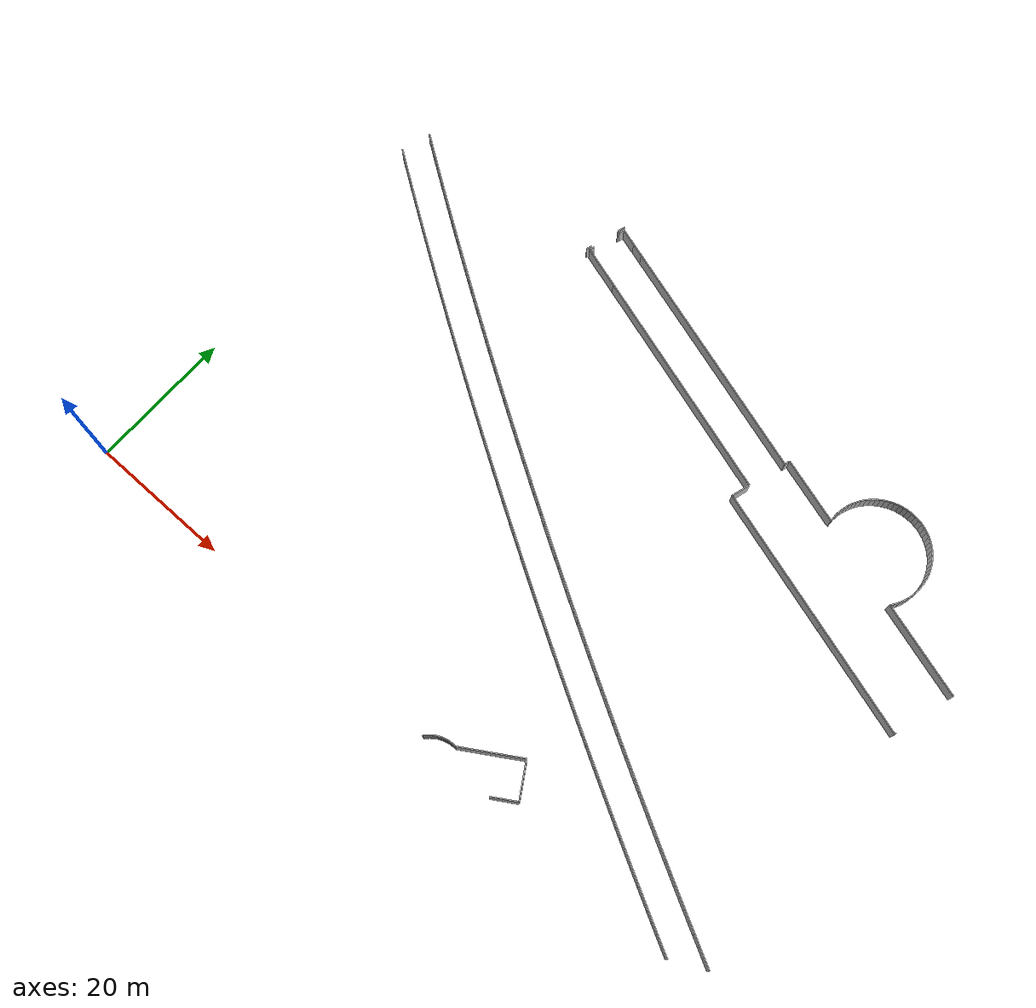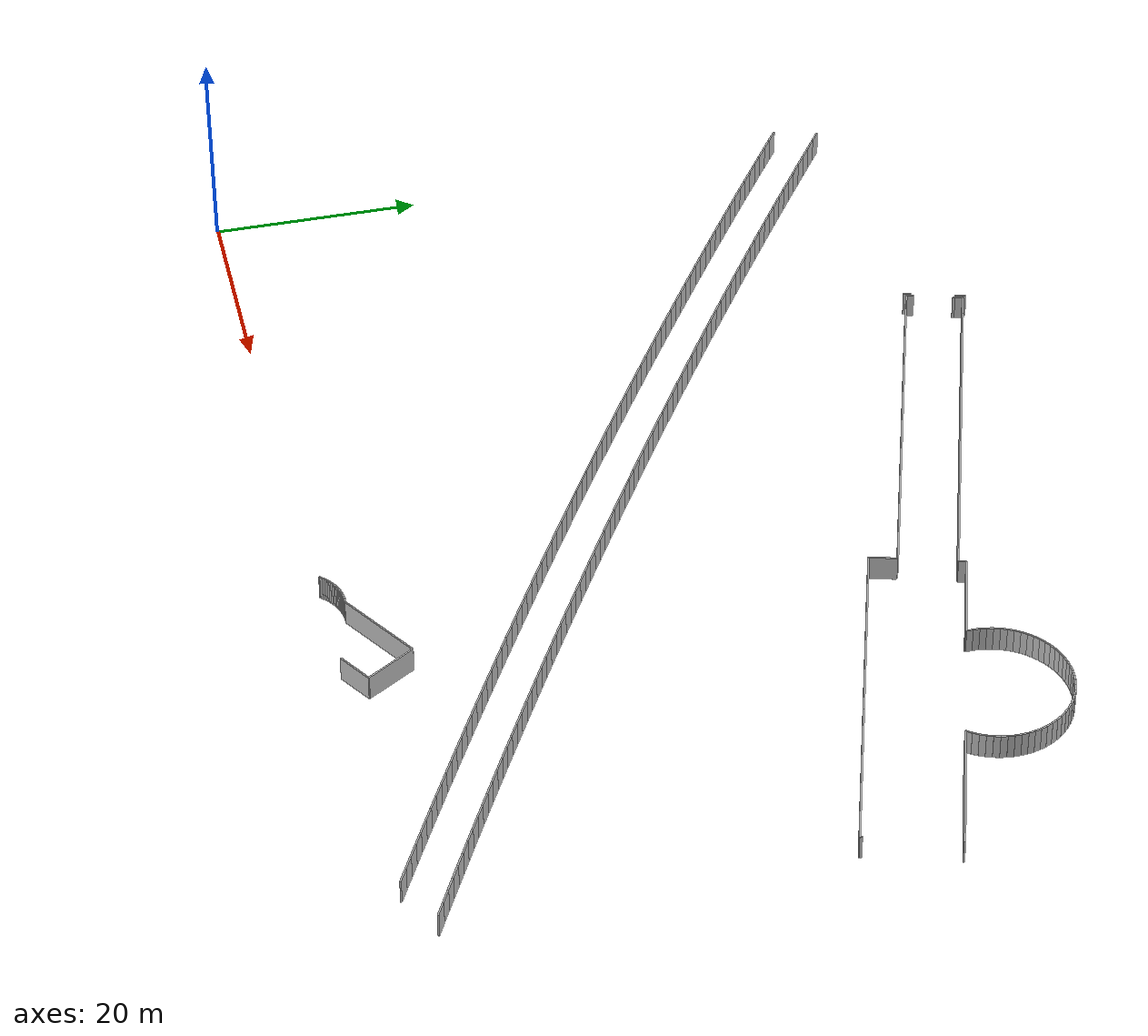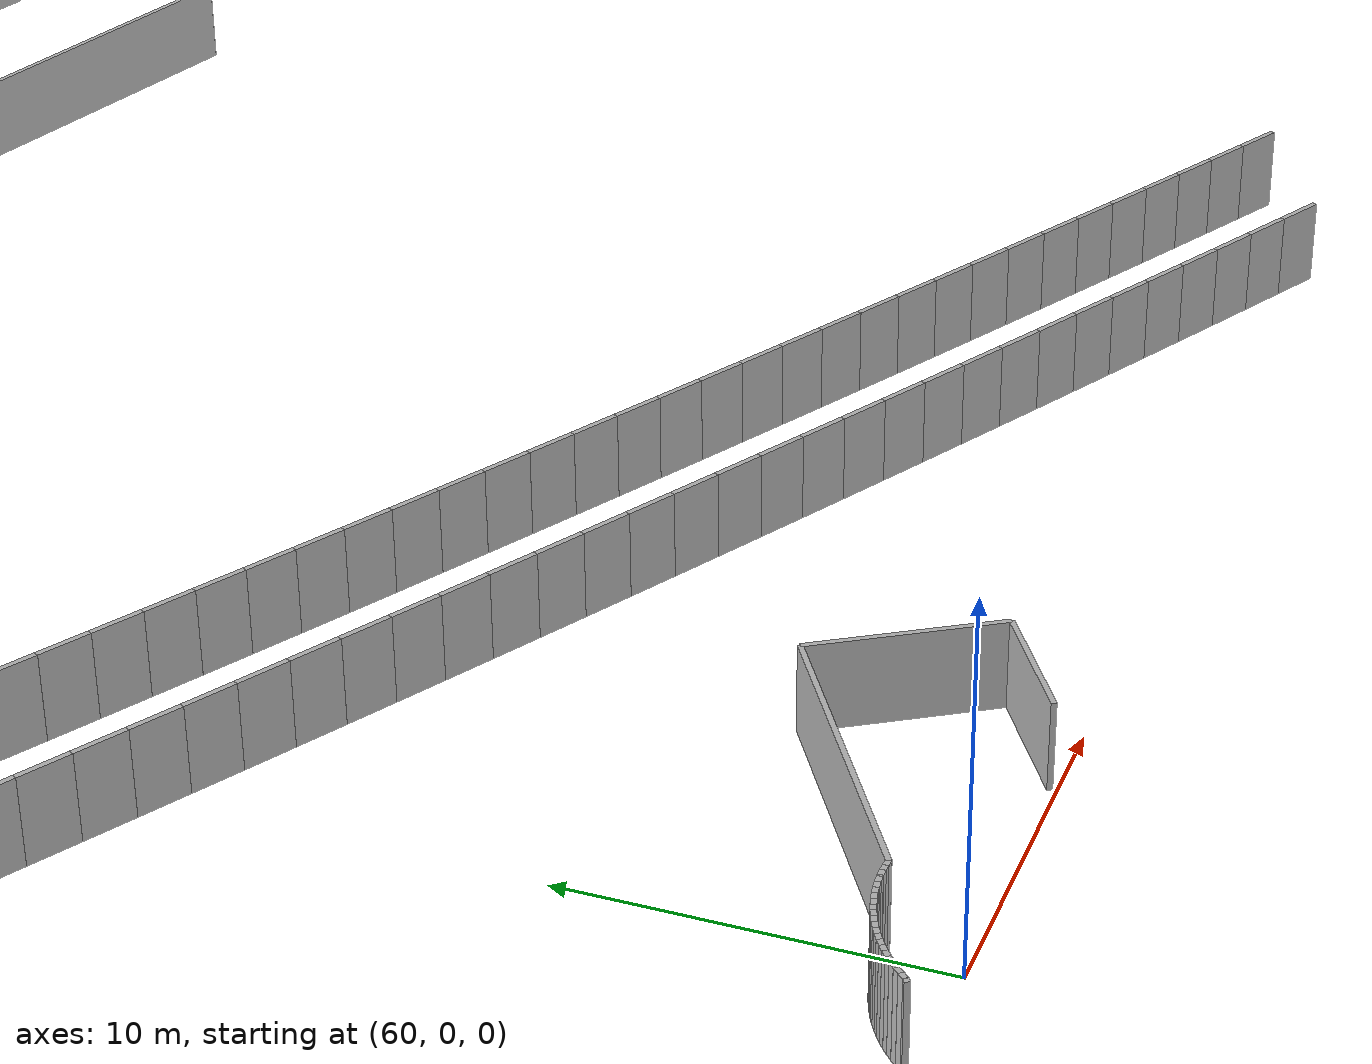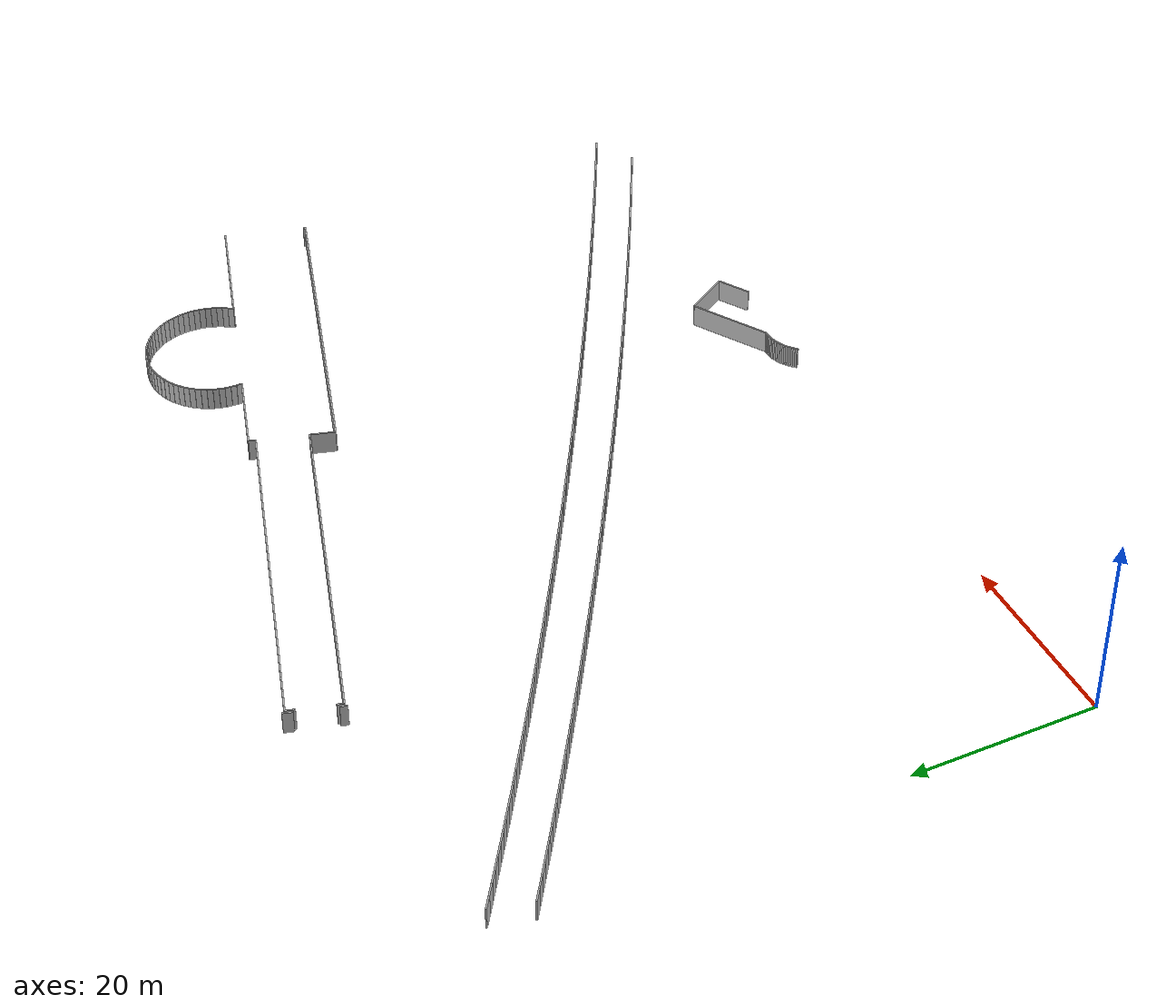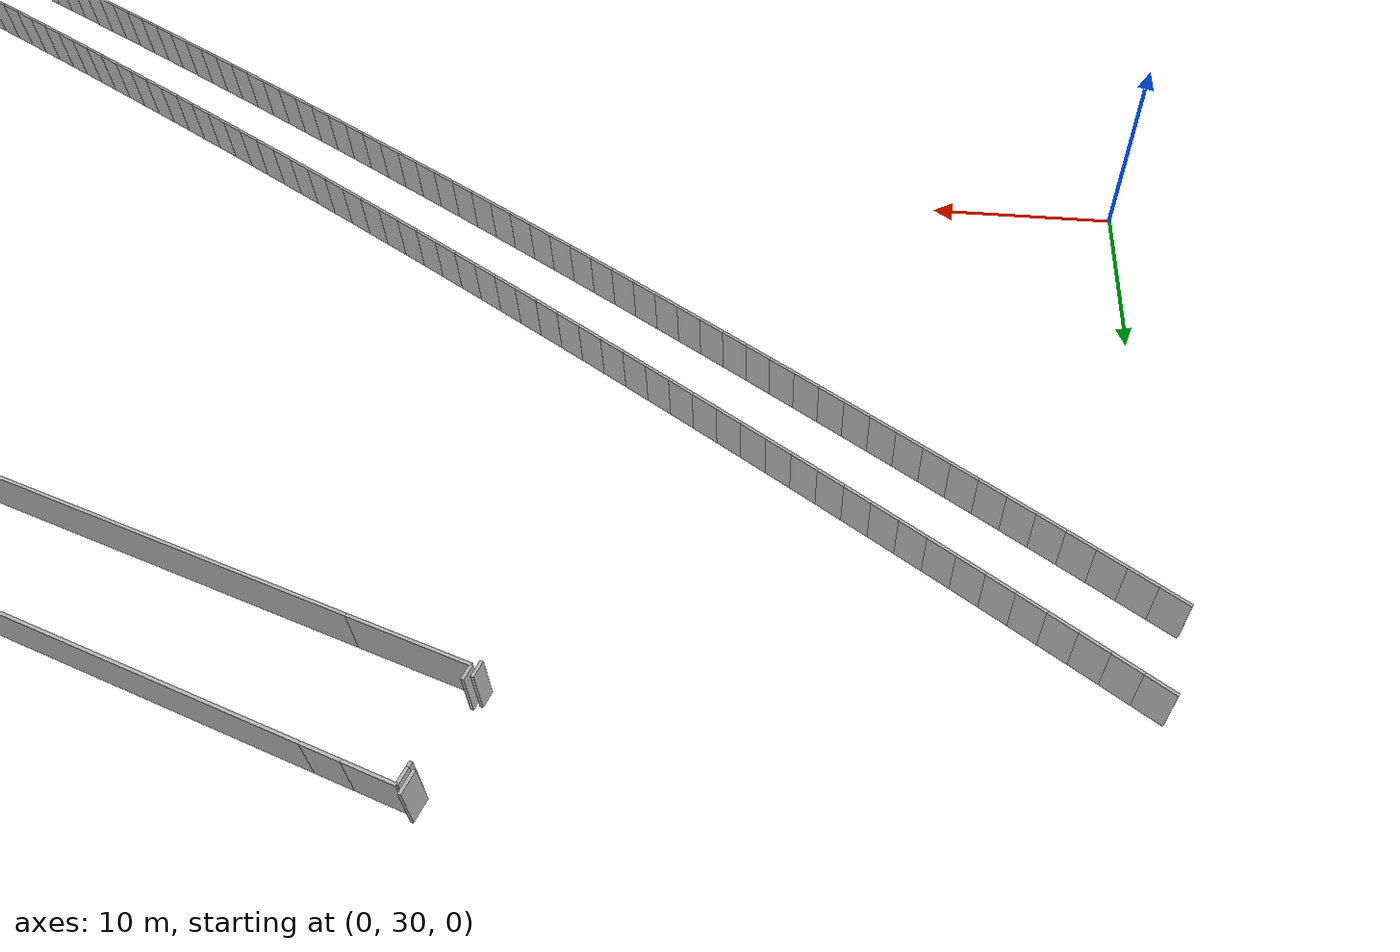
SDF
<?xml version="1.0" ?>
<sdf version="1.6">
  <model name="sps_0603">
    <pose frame="">0 0 0 0 -0 0</pose>
    <static>1</static>
    <self_collide>0</self_collide>
    <allow_auto_disable>0</allow_auto_disable>
    <link name="Wall8">
      <kinematic>0</kinematic>
      <gravity>1</gravity>
      <self_collide>0</self_collide>
      <collision name="collision">
        <geometry>
          <box>
            <size>1.06106 0.15 2.5</size>
          </box>
        </geometry>
        <pose frame="">0 0 0 0 -0 0</pose>
      </collision>
      <visual name="visual">
        <geometry>
          <box>
            <size>1.06106 0.15 2.5</size>
          </box>
        </geometry>
        <pose frame="">0 0 0 0 -0 0</pose>
        <cast_shadows>1</cast_shadows>
        <transparency>0.0</transparency>
      </visual>
      <pose frame="">29.9149 68.4915 1.25 0 0 -1.85665</pose>
    </link>
    <link name="Wall18">
      <kinematic>0</kinematic>
      <gravity>1</gravity>
      <self_collide>0</self_collide>
      <collision name="collision">
        <geometry>
          <box>
            <size>0.750779 0.15 2.5</size>
          </box>
        </geometry>
        <pose frame="">0 0 0 0 -0 0</pose>
      </collision>
      <visual name="visual">
        <geometry>
          <box>
            <size>0.750779 0.15 2.5</size>
          </box>
        </geometry>
        <pose frame="">0 0 0 0 -0 0</pose>
        <cast_shadows>1</cast_shadows>
        <transparency>0.0</transparency>
      </visual>
      <pose frame="">67.673 57.5155 1.25 0 -0 1.29894</pose>
    </link>
    <link name="Wall177">
      <kinematic>0</kinematic>
      <gravity>1</gravity>
      <self_collide>0</self_collide>
      <collision name="collision">
        <geometry>
          <box>
            <size>0.246796 0.15 2.5</size>
          </box>
        </geometry>
        <pose frame="">0 0 0 0 -0 0</pose>
      </collision>
      <visual name="visual">
        <geometry>
          <box>
            <size>0.246796 0.15 2.5</size>
          </box>
        </geometry>
        <pose frame="">0 0 0 0 -0 0</pose>
        <cast_shadows>1</cast_shadows>
        <transparency>0.0</transparency>
      </visual>
      <pose frame="">30.017 67.7747 1.25 0 -0 1.28545</pose>
    </link>
    <link name="Wall178">
      <kinematic>0</kinematic>
      <gravity>1</gravity>
      <self_collide>0</self_collide>
      <collision name="collision">
        <geometry>
          <box>
            <size>0.765576 0.15 2.5</size>
          </box>
        </geometry>
        <pose frame="">0 0 0 0 -0 0</pose>
      </collision>
      <visual name="visual">
        <geometry>
          <box>
            <size>0.765576 0.15 2.5</size>
          </box>
        </geometry>
        <pose frame="">0 0 0 0 -0 0</pose>
        <cast_shadows>1</cast_shadows>
        <transparency>0.0</transparency>
      </visual>
      <pose frame="">30.1595 68.2604 1.25 0 -0 1.28545</pose>
    </link>
    <link name="Wall277">
      <kinematic>0</kinematic>
      <gravity>1</gravity>
      <self_collide>0</self_collide>
      <collision name="collision">
        <geometry>
          <box>
            <size>2.64986 0.15 2.5</size>
          </box>
        </geometry>
        <pose frame="">0 0 0 0 -0 0</pose>
      </collision>
      <visual name="visual">
        <geometry>
          <box>
            <size>2.64986 0.15 2.5</size>
          </box>
        </geometry>
        <pose frame="">0 0 0 0 -0 0</pose>
        <cast_shadows>1</cast_shadows>
        <transparency>0.0</transparency>
      </visual>
      <pose frame="">65.5798 50.6267 1.25 0 -0 1.28343</pose>
    </link>
    <link name="Wall278">
      <kinematic>0</kinematic>
      <gravity>1</gravity>
      <self_collide>0</self_collide>
      <collision name="collision">
        <geometry>
          <box>
            <size>32.9414 0.15 2.5</size>
          </box>
        </geometry>
        <pose frame="">0 0 0 0 -0 0</pose>
      </collision>
      <visual name="visual">
        <geometry>
          <box>
            <size>32.9414 0.15 2.5</size>
          </box>
        </geometry>
        <pose frame="">0 0 0 0 -0 0</pose>
        <cast_shadows>1</cast_shadows>
        <transparency>0.0</transparency>
      </visual>
      <pose frame="">50.2124 56.7392 1.25 0 -0 2.84321</pose>
    </link>
    <link name="Wall279">
      <kinematic>0</kinematic>
      <gravity>1</gravity>
      <self_collide>0</self_collide>
      <collision name="collision">
        <geometry>
          <box>
            <size>6.01664 0.15 2.5</size>
          </box>
        </geometry>
        <pose frame="">0 0 0 0 -0 0</pose>
      </collision>
      <visual name="visual">
        <geometry>
          <box>
            <size>6.01664 0.15 2.5</size>
          </box>
        </geometry>
        <pose frame="">0 0 0 0 -0 0</pose>
        <cast_shadows>1</cast_shadows>
        <transparency>0.0</transparency>
      </visual>
      <pose frame="">31.594 62.4655 1.25 0 -0 2.84321</pose>
    </link>
    <link name="Wall338">
      <kinematic>0</kinematic>
      <gravity>1</gravity>
      <self_collide>0</self_collide>
      <collision name="collision">
        <geometry>
          <box>
            <size>0.779484 0.15 2.5</size>
          </box>
        </geometry>
        <pose frame="">0 0 0 0 -0 0</pose>
      </collision>
      <visual name="visual">
        <geometry>
          <box>
            <size>0.779484 0.15 2.5</size>
          </box>
        </geometry>
        <pose frame="">0 0 0 0 -0 0</pose>
        <cast_shadows>1</cast_shadows>
        <transparency>0.0</transparency>
      </visual>
      <pose frame="">28.4556 63.5212 1.25 0 -0 1.28471</pose>
    </link>
    <link name="Wall346">
      <kinematic>0</kinematic>
      <gravity>1</gravity>
      <self_collide>0</self_collide>
      <collision name="collision">
        <geometry>
          <box>
            <size>9.41379 0.15 2.5</size>
          </box>
        </geometry>
        <pose frame="">0 0 0 0 -0 0</pose>
      </collision>
      <visual name="visual">
        <geometry>
          <box>
            <size>9.41379 0.15 2.5</size>
          </box>
        </geometry>
        <pose frame="">0 0 0 0 -0 0</pose>
        <cast_shadows>1</cast_shadows>
        <transparency>0.0</transparency>
      </visual>
      <pose frame="">72.2803 56.5183 1.25 0 -0 2.84874</pose>
    </link>
    <link name="Wall348">
      <kinematic>0</kinematic>
      <gravity>1</gravity>
      <self_collide>0</self_collide>
      <collision name="collision">
        <geometry>
          <box>
            <size>13.6171 0.15 2.5</size>
          </box>
        </geometry>
        <pose frame="">0 0 0 0 -0 0</pose>
      </collision>
      <visual name="visual">
        <geometry>
          <box>
            <size>13.6171 0.15 2.5</size>
          </box>
        </geometry>
        <pose frame="">0 0 0 0 -0 0</pose>
        <cast_shadows>1</cast_shadows>
        <transparency>0.0</transparency>
      </visual>
      <pose frame="">95.7215 49.4496 1.25 0 -0 2.84871</pose>
    </link>
    <link name="Wall422">
      <kinematic>0</kinematic>
      <gravity>1</gravity>
      <self_collide>0</self_collide>
      <collision name="collision">
        <geometry>
          <box>
            <size>0.728133 0.15 2.5</size>
          </box>
        </geometry>
        <pose frame="">0 0 0 0 -0 0</pose>
      </collision>
      <visual name="visual">
        <geometry>
          <box>
            <size>0.728133 0.15 2.5</size>
          </box>
        </geometry>
        <pose frame="">0 0 0 0 -0 0</pose>
        <cast_shadows>1</cast_shadows>
        <transparency>0.0</transparency>
      </visual>
      <pose frame="">28.8209 63.6993 1.25 0 -0 1.28624</pose>
    </link>
    <link name="Wall521">
      <kinematic>0</kinematic>
      <gravity>1</gravity>
      <self_collide>0</self_collide>
      <collision name="collision">
        <geometry>
          <box>
            <size>0.246303 0.15 2.5</size>
          </box>
        </geometry>
        <pose frame="">0 0 0 0 -0 0</pose>
      </collision>
      <visual name="visual">
        <geometry>
          <box>
            <size>0.246303 0.15 2.5</size>
          </box>
        </geometry>
        <pose frame="">0 0 0 0 -0 0</pose>
        <cast_shadows>1</cast_shadows>
        <transparency>0.0</transparency>
      </visual>
      <pose frame="">99.7046 39.0806 1.25 0 0 -1.86418</pose>
    </link>
    <link name="Wall599">
      <kinematic>0</kinematic>
      <gravity>1</gravity>
      <self_collide>0</self_collide>
      <collision name="collision">
        <geometry>
          <box>
            <size>2.4989 0.15 2.5</size>
          </box>
        </geometry>
        <pose frame="">0 0 0 0 -0 0</pose>
      </collision>
      <visual name="visual">
        <geometry>
          <box>
            <size>2.4989 0.15 2.5</size>
          </box>
        </geometry>
        <pose frame="">0 0 0 0 -0 0</pose>
        <cast_shadows>1</cast_shadows>
        <transparency>0.0</transparency>
      </visual>
      <pose frame="">31.4615 68.2604 1.25 0 0 -0.298385</pose>
    </link>
    <link name="Wall600">
      <kinematic>0</kinematic>
      <gravity>1</gravity>
      <self_collide>0</self_collide>
      <collision name="collision">
        <geometry>
          <box>
            <size>1.89758 0.15 2.5</size>
          </box>
        </geometry>
        <pose frame="">0 0 0 0 -0 0</pose>
      </collision>
      <visual name="visual">
        <geometry>
          <box>
            <size>1.89758 0.15 2.5</size>
          </box>
        </geometry>
        <pose frame="">0 0 0 0 -0 0</pose>
        <cast_shadows>1</cast_shadows>
        <transparency>0.0</transparency>
      </visual>
      <pose frame="">33.5626 67.6142 1.25 0 0 -0.298385</pose>
    </link>
    <link name="Wall601">
      <kinematic>0</kinematic>
      <gravity>1</gravity>
      <self_collide>0</self_collide>
      <collision name="collision">
        <geometry>
          <box>
            <size>34.6331 0.15 2.5</size>
          </box>
        </geometry>
        <pose frame="">0 0 0 0 -0 0</pose>
      </collision>
      <visual name="visual">
        <geometry>
          <box>
            <size>34.6331 0.15 2.5</size>
          </box>
        </geometry>
        <pose frame="">0 0 0 0 -0 0</pose>
        <cast_shadows>1</cast_shadows>
        <transparency>0.0</transparency>
      </visual>
      <pose frame="">51.0208 62.2446 1.25 0 0 -0.298385</pose>
    </link>
    <link name="Wall605">
      <kinematic>0</kinematic>
      <gravity>1</gravity>
      <self_collide>0</self_collide>
      <collision name="collision">
        <geometry>
          <box>
            <size>15.8757 0.15 2.5</size>
          </box>
        </geometry>
        <pose frame="">0 0 0 0 -0 0</pose>
      </collision>
      <visual name="visual">
        <geometry>
          <box>
            <size>15.8757 0.15 2.5</size>
          </box>
        </geometry>
        <pose frame="">0 0 0 0 -0 0</pose>
        <cast_shadows>1</cast_shadows>
        <transparency>0.0</transparency>
      </visual>
      <pose frame="">92.0692 41.2546 1.25 0 -0 2.8487</pose>
    </link>
    <link name="Wall606">
      <kinematic>0</kinematic>
      <gravity>1</gravity>
      <self_collide>0</self_collide>
      <collision name="collision">
        <geometry>
          <box>
            <size>20.1221 0.15 2.5</size>
          </box>
        </geometry>
        <pose frame="">0 0 0 0 -0 0</pose>
      </collision>
      <visual name="visual">
        <geometry>
          <box>
            <size>20.1221 0.15 2.5</size>
          </box>
        </geometry>
        <pose frame="">0 0 0 0 -0 0</pose>
        <cast_shadows>1</cast_shadows>
        <transparency>0.0</transparency>
      </visual>
      <pose frame="">74.8368 46.4512 1.25 0 -0 2.8487</pose>
    </link>
    <link name="Wall2468">
      <kinematic>0</kinematic>
      <gravity>1</gravity>
      <self_collide>0</self_collide>
      <collision name="collision">
        <geometry>
          <box>
            <size>3.67519 0.15 2.5</size>
          </box>
        </geometry>
        <pose frame="">0 0 0 0 -0 0</pose>
      </collision>
      <visual name="visual">
        <geometry>
          <box>
            <size>3.67519 0.15 2.5</size>
          </box>
        </geometry>
        <pose frame="">0 0 0 0 -0 0</pose>
        <cast_shadows>1</cast_shadows>
        <transparency>0.0</transparency>
      </visual>
      <pose frame="">69.1415 1.16109 1.25 0 0 -2.58435</pose>
    </link>
    <link name="Wall2512">
      <kinematic>0</kinematic>
      <gravity>1</gravity>
      <self_collide>0</self_collide>
      <collision name="collision">
        <geometry>
          <box>
            <size>0.130798 0.15 2.5</size>
          </box>
        </geometry>
        <pose frame="">0 0 0 0 -0 0</pose>
      </collision>
      <visual name="visual">
        <geometry>
          <box>
            <size>0.130798 0.15 2.5</size>
          </box>
        </geometry>
        <pose frame="">0 0 0 0 -0 0</pose>
        <cast_shadows>1</cast_shadows>
        <transparency>0.0</transparency>
      </visual>
      <pose frame="">56.5082 0.300887 1.25 0 -0 0.557066</pose>
    </link>
    <link name="Wall2513">
      <kinematic>0</kinematic>
      <gravity>1</gravity>
      <self_collide>0</self_collide>
      <collision name="collision">
        <geometry>
          <box>
            <size>0.205358 0.15 2.5</size>
          </box>
        </geometry>
        <pose frame="">0 0 0 0 -0 0</pose>
      </collision>
      <visual name="visual">
        <geometry>
          <box>
            <size>0.205358 0.15 2.5</size>
          </box>
        </geometry>
        <pose frame="">0 0 0 0 -0 0</pose>
        <cast_shadows>1</cast_shadows>
        <transparency>0.0</transparency>
      </visual>
      <pose frame="">56.6314 0.412673 1.25 0 -0 0.851016</pose>
    </link>
    <link name="Wall2514">
      <kinematic>0</kinematic>
      <gravity>1</gravity>
      <self_collide>0</self_collide>
      <collision name="collision">
        <geometry>
          <box>
            <size>0.20509 0.15 2.5</size>
          </box>
        </geometry>
        <pose frame="">0 0 0 0 -0 0</pose>
      </collision>
      <visual name="visual">
        <geometry>
          <box>
            <size>0.20509 0.15 2.5</size>
          </box>
        </geometry>
        <pose frame="">0 0 0 0 -0 0</pose>
        <cast_shadows>1</cast_shadows>
        <transparency>0.0</transparency>
      </visual>
      <pose frame="">56.77 0.563888 1.25 0 -0 0.806233</pose>
    </link>
    <link name="Wall2515">
      <kinematic>0</kinematic>
      <gravity>1</gravity>
      <self_collide>0</self_collide>
      <collision name="collision">
        <geometry>
          <box>
            <size>0.205411 0.15 2.5</size>
          </box>
        </geometry>
        <pose frame="">0 0 0 0 -0 0</pose>
      </collision>
      <visual name="visual">
        <geometry>
          <box>
            <size>0.205411 0.15 2.5</size>
          </box>
        </geometry>
        <pose frame="">0 0 0 0 -0 0</pose>
        <cast_shadows>1</cast_shadows>
        <transparency>0.0</transparency>
      </visual>
      <pose frame="">56.9154 0.708693 1.25 0 -0 0.760603</pose>
    </link>
    <link name="Wall2516">
      <kinematic>0</kinematic>
      <gravity>1</gravity>
      <self_collide>0</self_collide>
      <collision name="collision">
        <geometry>
          <box>
            <size>0.205158 0.15 2.5</size>
          </box>
        </geometry>
        <pose frame="">0 0 0 0 -0 0</pose>
      </collision>
      <visual name="visual">
        <geometry>
          <box>
            <size>0.205158 0.15 2.5</size>
          </box>
        </geometry>
        <pose frame="">0 0 0 0 -0 0</pose>
        <cast_shadows>1</cast_shadows>
        <transparency>0.0</transparency>
      </visual>
      <pose frame="">57.0673 0.846785 1.25 0 -0 0.7155</pose>
    </link>
    <link name="Wall2517">
      <kinematic>0</kinematic>
      <gravity>1</gravity>
      <self_collide>0</self_collide>
      <collision name="collision">
        <geometry>
          <box>
            <size>0.205152 0.15 2.5</size>
          </box>
        </geometry>
        <pose frame="">0 0 0 0 -0 0</pose>
      </collision>
      <visual name="visual">
        <geometry>
          <box>
            <size>0.205152 0.15 2.5</size>
          </box>
        </geometry>
        <pose frame="">0 0 0 0 -0 0</pose>
        <cast_shadows>1</cast_shadows>
        <transparency>0.0</transparency>
      </visual>
      <pose frame="">57.2251 0.977797 1.25 0 -0 0.67028</pose>
    </link>
    <link name="Wall2518">
      <kinematic>0</kinematic>
      <gravity>1</gravity>
      <self_collide>0</self_collide>
      <collision name="collision">
        <geometry>
          <box>
            <size>0.205097 0.15 2.5</size>
          </box>
        </geometry>
        <pose frame="">0 0 0 0 -0 0</pose>
      </collision>
      <visual name="visual">
        <geometry>
          <box>
            <size>0.205097 0.15 2.5</size>
          </box>
        </geometry>
        <pose frame="">0 0 0 0 -0 0</pose>
        <cast_shadows>1</cast_shadows>
        <transparency>0.0</transparency>
      </visual>
      <pose frame="">57.3885 1.10161 1.25 0 -0 0.626061</pose>
    </link>
    <link name="Wall2519">
      <kinematic>0</kinematic>
      <gravity>1</gravity>
      <self_collide>0</self_collide>
      <collision name="collision">
        <geometry>
          <box>
            <size>0.205175 0.15 2.5</size>
          </box>
        </geometry>
        <pose frame="">0 0 0 0 -0 0</pose>
      </collision>
      <visual name="visual">
        <geometry>
          <box>
            <size>0.205175 0.15 2.5</size>
          </box>
        </geometry>
        <pose frame="">0 0 0 0 -0 0</pose>
        <cast_shadows>1</cast_shadows>
        <transparency>0.0</transparency>
      </visual>
      <pose frame="">57.5575 1.21791 1.25 0 -0 0.579917</pose>
    </link>
    <link name="Wall2520">
      <kinematic>0</kinematic>
      <gravity>1</gravity>
      <self_collide>0</self_collide>
      <collision name="collision">
        <geometry>
          <box>
            <size>0.205332 0.15 2.5</size>
          </box>
        </geometry>
        <pose frame="">0 0 0 0 -0 0</pose>
      </collision>
      <visual name="visual">
        <geometry>
          <box>
            <size>0.205332 0.15 2.5</size>
          </box>
        </geometry>
        <pose frame="">0 0 0 0 -0 0</pose>
        <cast_shadows>1</cast_shadows>
        <transparency>0.0</transparency>
      </visual>
      <pose frame="">57.7316 1.32652 1.25 0 -0 0.535628</pose>
    </link>
    <link name="Wall2521">
      <kinematic>0</kinematic>
      <gravity>1</gravity>
      <self_collide>0</self_collide>
      <collision name="collision">
        <geometry>
          <box>
            <size>0.205171 0.15 2.5</size>
          </box>
        </geometry>
        <pose frame="">0 0 0 0 -0 0</pose>
      </collision>
      <visual name="visual">
        <geometry>
          <box>
            <size>0.205171 0.15 2.5</size>
          </box>
        </geometry>
        <pose frame="">0 0 0 0 -0 0</pose>
        <cast_shadows>1</cast_shadows>
        <transparency>0.0</transparency>
      </visual>
      <pose frame="">57.9104 1.4272 1.25 0 -0 0.489992</pose>
    </link>
    <link name="Wall2522">
      <kinematic>0</kinematic>
      <gravity>1</gravity>
      <self_collide>0</self_collide>
      <collision name="collision">
        <geometry>
          <box>
            <size>0.205276 0.15 2.5</size>
          </box>
        </geometry>
        <pose frame="">0 0 0 0 -0 0</pose>
      </collision>
      <visual name="visual">
        <geometry>
          <box>
            <size>0.205276 0.15 2.5</size>
          </box>
        </geometry>
        <pose frame="">0 0 0 0 -0 0</pose>
        <cast_shadows>1</cast_shadows>
        <transparency>0.0</transparency>
      </visual>
      <pose frame="">58.0936 1.51958 1.25 0 -0 0.4441</pose>
    </link>
    <link name="Wall2523">
      <kinematic>0</kinematic>
      <gravity>1</gravity>
      <self_collide>0</self_collide>
      <collision name="collision">
        <geometry>
          <box>
            <size>0.205096 0.15 2.5</size>
          </box>
        </geometry>
        <pose frame="">0 0 0 0 -0 0</pose>
      </collision>
      <visual name="visual">
        <geometry>
          <box>
            <size>0.205096 0.15 2.5</size>
          </box>
        </geometry>
        <pose frame="">0 0 0 0 -0 0</pose>
        <cast_shadows>1</cast_shadows>
        <transparency>0.0</transparency>
      </visual>
      <pose frame="">58.2807 1.60368 1.25 0 -0 0.400789</pose>
    </link>
    <link name="Wall2524">
      <kinematic>0</kinematic>
      <gravity>1</gravity>
      <self_collide>0</self_collide>
      <collision name="collision">
        <geometry>
          <box>
            <size>0.205381 0.15 2.5</size>
          </box>
        </geometry>
        <pose frame="">0 0 0 0 -0 0</pose>
      </collision>
      <visual name="visual">
        <geometry>
          <box>
            <size>0.205381 0.15 2.5</size>
          </box>
        </geometry>
        <pose frame="">0 0 0 0 -0 0</pose>
        <cast_shadows>1</cast_shadows>
        <transparency>0.0</transparency>
      </visual>
      <pose frame="">58.4714 1.6794 1.25 0 -0 0.355119</pose>
    </link>
    <link name="Wall2525">
      <kinematic>0</kinematic>
      <gravity>1</gravity>
      <self_collide>0</self_collide>
      <collision name="collision">
        <geometry>
          <box>
            <size>0.205148 0.15 2.5</size>
          </box>
        </geometry>
        <pose frame="">0 0 0 0 -0 0</pose>
      </collision>
      <visual name="visual">
        <geometry>
          <box>
            <size>0.205148 0.15 2.5</size>
          </box>
        </geometry>
        <pose frame="">0 0 0 0 -0 0</pose>
        <cast_shadows>1</cast_shadows>
        <transparency>0.0</transparency>
      </visual>
      <pose frame="">58.6654 1.74629 1.25 0 -0 0.308955</pose>
    </link>
    <link name="Wall2526">
      <kinematic>0</kinematic>
      <gravity>1</gravity>
      <self_collide>0</self_collide>
      <collision name="collision">
        <geometry>
          <box>
            <size>0.205122 0.15 2.5</size>
          </box>
        </geometry>
        <pose frame="">0 0 0 0 -0 0</pose>
      </collision>
      <visual name="visual">
        <geometry>
          <box>
            <size>0.205122 0.15 2.5</size>
          </box>
        </geometry>
        <pose frame="">0 0 0 0 -0 0</pose>
        <cast_shadows>1</cast_shadows>
        <transparency>0.0</transparency>
      </visual>
      <pose frame="">58.8621 1.80427 1.25 0 -0 0.264321</pose>
    </link>
    <link name="Wall2527">
      <kinematic>0</kinematic>
      <gravity>1</gravity>
      <self_collide>0</self_collide>
      <collision name="collision">
        <geometry>
          <box>
            <size>0.205147 0.15 2.5</size>
          </box>
        </geometry>
        <pose frame="">0 0 0 0 -0 0</pose>
      </collision>
      <visual name="visual">
        <geometry>
          <box>
            <size>0.205147 0.15 2.5</size>
          </box>
        </geometry>
        <pose frame="">0 0 0 0 -0 0</pose>
        <cast_shadows>1</cast_shadows>
        <transparency>0.0</transparency>
      </visual>
      <pose frame="">59.0612 1.85347 1.25 0 -0 0.220153</pose>
    </link>
    <link name="Wall2528">
      <kinematic>0</kinematic>
      <gravity>1</gravity>
      <self_collide>0</self_collide>
      <collision name="collision">
        <geometry>
          <box>
            <size>0.205267 0.15 2.5</size>
          </box>
        </geometry>
        <pose frame="">0 0 0 0 -0 0</pose>
      </collision>
      <visual name="visual">
        <geometry>
          <box>
            <size>0.205267 0.15 2.5</size>
          </box>
        </geometry>
        <pose frame="">0 0 0 0 -0 0</pose>
        <cast_shadows>1</cast_shadows>
        <transparency>0.0</transparency>
      </visual>
      <pose frame="">59.2624 1.89369 1.25 0 -0 0.174534</pose>
    </link>
    <link name="Wall2529">
      <kinematic>0</kinematic>
      <gravity>1</gravity>
      <self_collide>0</self_collide>
      <collision name="collision">
        <geometry>
          <box>
            <size>0.205313 0.15 2.5</size>
          </box>
        </geometry>
        <pose frame="">0 0 0 0 -0 0</pose>
      </collision>
      <visual name="visual">
        <geometry>
          <box>
            <size>0.205313 0.15 2.5</size>
          </box>
        </geometry>
        <pose frame="">0 0 0 0 -0 0</pose>
        <cast_shadows>1</cast_shadows>
        <transparency>0.0</transparency>
      </visual>
      <pose frame="">59.4652 1.9247 1.25 0 -0 0.12878</pose>
    </link>
    <link name="Wall2530">
      <kinematic>0</kinematic>
      <gravity>1</gravity>
      <self_collide>0</self_collide>
      <collision name="collision">
        <geometry>
          <box>
            <size>0.205328 0.15 2.5</size>
          </box>
        </geometry>
        <pose frame="">0 0 0 0 -0 0</pose>
      </collision>
      <visual name="visual">
        <geometry>
          <box>
            <size>0.205328 0.15 2.5</size>
          </box>
        </geometry>
        <pose frame="">0 0 0 0 -0 0</pose>
        <cast_shadows>1</cast_shadows>
        <transparency>0.0</transparency>
      </visual>
      <pose frame="">59.6693 1.94658 1.25 0 -0 0.0848199</pose>
    </link>
    <link name="Wall2531">
      <kinematic>0</kinematic>
      <gravity>1</gravity>
      <self_collide>0</self_collide>
      <collision name="collision">
        <geometry>
          <box>
            <size>0.0512757 0.15 2.5</size>
          </box>
        </geometry>
        <pose frame="">0 0 0 0 -0 0</pose>
      </collision>
      <visual name="visual">
        <geometry>
          <box>
            <size>0.0512757 0.15 2.5</size>
          </box>
        </geometry>
        <pose frame="">0 0 0 0 -0 0</pose>
        <cast_shadows>1</cast_shadows>
        <transparency>0.0</transparency>
      </visual>
      <pose frame="">59.7972 1.95659 1.25 0 -0 0.0512067</pose>
    </link>
    <link name="Wall2532">
      <kinematic>0</kinematic>
      <gravity>1</gravity>
      <self_collide>0</self_collide>
      <collision name="collision">
        <geometry>
          <box>
            <size>0.188316 0.15 2.5</size>
          </box>
        </geometry>
        <pose frame="">0 0 0 0 -0 0</pose>
      </collision>
      <visual name="visual">
        <geometry>
          <box>
            <size>0.188316 0.15 2.5</size>
          </box>
        </geometry>
        <pose frame="">0 0 0 0 -0 0</pose>
        <cast_shadows>1</cast_shadows>
        <transparency>0.0</transparency>
      </visual>
      <pose frame="">59.917 1.96071 1.25 0 -0 0.0298225</pose>
    </link>
    <link name="Wall2533">
      <kinematic>0</kinematic>
      <gravity>1</gravity>
      <self_collide>0</self_collide>
      <collision name="collision">
        <geometry>
          <box>
            <size>0.188004 0.15 2.5</size>
          </box>
        </geometry>
        <pose frame="">0 0 0 0 -0 0</pose>
      </collision>
      <visual name="visual">
        <geometry>
          <box>
            <size>0.188004 0.15 2.5</size>
          </box>
        </geometry>
        <pose frame="">0 0 0 0 -0 0</pose>
        <cast_shadows>1</cast_shadows>
        <transparency>0.0</transparency>
      </visual>
      <pose frame="">60.1051 1.96229 1.25 0 0 -0.0129863</pose>
    </link>
    <link name="Wall2534">
      <kinematic>0</kinematic>
      <gravity>1</gravity>
      <self_collide>0</self_collide>
      <collision name="collision">
        <geometry>
          <box>
            <size>0.188059 0.15 2.5</size>
          </box>
        </geometry>
        <pose frame="">0 0 0 0 -0 0</pose>
      </collision>
      <visual name="visual">
        <geometry>
          <box>
            <size>0.188059 0.15 2.5</size>
          </box>
        </geometry>
        <pose frame="">0 0 0 0 -0 0</pose>
        <cast_shadows>1</cast_shadows>
        <transparency>0.0</transparency>
      </visual>
      <pose frame="">60.293 1.95619 1.25 0 0 -0.0519519</pose>
    </link>
    <link name="Wall2535">
      <kinematic>0</kinematic>
      <gravity>1</gravity>
      <self_collide>0</self_collide>
      <collision name="collision">
        <geometry>
          <box>
            <size>8.85031 0.15 2.5</size>
          </box>
        </geometry>
        <pose frame="">0 0 0 0 -0 0</pose>
      </collision>
      <visual name="visual">
        <geometry>
          <box>
            <size>8.85031 0.15 2.5</size>
          </box>
        </geometry>
        <pose frame="">0 0 0 0 -0 0</pose>
        <cast_shadows>1</cast_shadows>
        <transparency>0.0</transparency>
      </visual>
      <pose frame="">64.1428 4.29109 1.25 0 -0 0.557123</pose>
    </link>
    <link name="Wall2536">
      <kinematic>0</kinematic>
      <gravity>1</gravity>
      <self_collide>0</self_collide>
      <collision name="collision">
        <geometry>
          <box>
            <size>5.29948 0.15 2.5</size>
          </box>
        </geometry>
        <pose frame="">0 0 0 0 -0 0</pose>
      </collision>
      <visual name="visual">
        <geometry>
          <box>
            <size>5.29948 0.15 2.5</size>
          </box>
        </geometry>
        <pose frame="">0 0 0 0 -0 0</pose>
        <cast_shadows>1</cast_shadows>
        <transparency>0.0</transparency>
      </visual>
      <pose frame="">69.2999 4.38188 1.25 0 0 -1.01364</pose>
    </link>
    <link name="Wall4809">
      <kinematic>0</kinematic>
      <gravity>1</gravity>
      <self_collide>0</self_collide>
      <collision name="collision">
        <geometry>
          <box>
            <size>0.623304 0.15 2.5</size>
          </box>
        </geometry>
        <pose frame="">0 0 0 0 -0 0</pose>
      </collision>
      <visual name="visual">
        <geometry>
          <box>
            <size>0.623304 0.15 2.5</size>
          </box>
        </geometry>
        <pose frame="">0 0 0 0 -0 0</pose>
        <cast_shadows>1</cast_shadows>
        <transparency>0.0</transparency>
      </visual>
      <pose frame="">86.0643 62.4152 1.25 0 0 -0.332465</pose>
    </link>
    <link name="Wall4810">
      <kinematic>0</kinematic>
      <gravity>1</gravity>
      <self_collide>0</self_collide>
      <collision name="collision">
        <geometry>
          <box>
            <size>0.62325 0.15 2.5</size>
          </box>
        </geometry>
        <pose frame="">0 0 0 0 -0 0</pose>
      </collision>
      <visual name="visual">
        <geometry>
          <box>
            <size>0.62325 0.15 2.5</size>
          </box>
        </geometry>
        <pose frame="">0 0 0 0 -0 0</pose>
        <cast_shadows>1</cast_shadows>
        <transparency>0.0</transparency>
      </visual>
      <pose frame="">86.6431 62.1857 1.25 0 0 -0.422599</pose>
    </link>
    <link name="Wall4811">
      <kinematic>0</kinematic>
      <gravity>1</gravity>
      <self_collide>0</self_collide>
      <collision name="collision">
        <geometry>
          <box>
            <size>0.623227 0.15 2.5</size>
          </box>
        </geometry>
        <pose frame="">0 0 0 0 -0 0</pose>
      </collision>
      <visual name="visual">
        <geometry>
          <box>
            <size>0.623227 0.15 2.5</size>
          </box>
        </geometry>
        <pose frame="">0 0 0 0 -0 0</pose>
        <cast_shadows>1</cast_shadows>
        <transparency>0.0</transparency>
      </visual>
      <pose frame="">87.199 61.9053 1.25 0 0 -0.511712</pose>
    </link>
    <link name="Wall4812">
      <kinematic>0</kinematic>
      <gravity>1</gravity>
      <self_collide>0</self_collide>
      <collision name="collision">
        <geometry>
          <box>
            <size>0.623388 0.15 2.5</size>
          </box>
        </geometry>
        <pose frame="">0 0 0 0 -0 0</pose>
      </collision>
      <visual name="visual">
        <geometry>
          <box>
            <size>0.623388 0.15 2.5</size>
          </box>
        </geometry>
        <pose frame="">0 0 0 0 -0 0</pose>
        <cast_shadows>1</cast_shadows>
        <transparency>0.0</transparency>
      </visual>
      <pose frame="">87.7276 61.5762 1.25 0 0 -0.602015</pose>
    </link>
    <link name="Wall4813">
      <kinematic>0</kinematic>
      <gravity>1</gravity>
      <self_collide>0</self_collide>
      <collision name="collision">
        <geometry>
          <box>
            <size>0.623144 0.15 2.5</size>
          </box>
        </geometry>
        <pose frame="">0 0 0 0 -0 0</pose>
      </collision>
      <visual name="visual">
        <geometry>
          <box>
            <size>0.623144 0.15 2.5</size>
          </box>
        </geometry>
        <pose frame="">0 0 0 0 -0 0</pose>
        <cast_shadows>1</cast_shadows>
        <transparency>0.0</transparency>
      </visual>
      <pose frame="">88.2244 61.201 1.25 0 0 -0.691553</pose>
    </link>
    <link name="Wall4814">
      <kinematic>0</kinematic>
      <gravity>1</gravity>
      <self_collide>0</self_collide>
      <collision name="collision">
        <geometry>
          <box>
            <size>0.623126 0.15 2.5</size>
          </box>
        </geometry>
        <pose frame="">0 0 0 0 -0 0</pose>
      </collision>
      <visual name="visual">
        <geometry>
          <box>
            <size>0.623126 0.15 2.5</size>
          </box>
        </geometry>
        <pose frame="">0 0 0 0 -0 0</pose>
        <cast_shadows>1</cast_shadows>
        <transparency>0.0</transparency>
      </visual>
      <pose frame="">88.6857 60.7829 1.25 0 0 -0.781242</pose>
    </link>
    <link name="Wall4815">
      <kinematic>0</kinematic>
      <gravity>1</gravity>
      <self_collide>0</self_collide>
      <collision name="collision">
        <geometry>
          <box>
            <size>0.623368 0.15 2.5</size>
          </box>
        </geometry>
        <pose frame="">0 0 0 0 -0 0</pose>
      </collision>
      <visual name="visual">
        <geometry>
          <box>
            <size>0.623368 0.15 2.5</size>
          </box>
        </geometry>
        <pose frame="">0 0 0 0 -0 0</pose>
        <cast_shadows>1</cast_shadows>
        <transparency>0.0</transparency>
      </visual>
      <pose frame="">89.1077 60.3251 1.25 0 0 -0.870868</pose>
    </link>
    <link name="Wall4816">
      <kinematic>0</kinematic>
      <gravity>1</gravity>
      <self_collide>0</self_collide>
      <collision name="collision">
        <geometry>
          <box>
            <size>0.62334 0.15 2.5</size>
          </box>
        </geometry>
        <pose frame="">0 0 0 0 -0 0</pose>
      </collision>
      <visual name="visual">
        <geometry>
          <box>
            <size>0.62334 0.15 2.5</size>
          </box>
        </geometry>
        <pose frame="">0 0 0 0 -0 0</pose>
        <cast_shadows>1</cast_shadows>
        <transparency>0.0</transparency>
      </visual>
      <pose frame="">89.4869 59.8312 1.25 0 0 -0.960985</pose>
    </link>
    <link name="Wall4817">
      <kinematic>0</kinematic>
      <gravity>1</gravity>
      <self_collide>0</self_collide>
      <collision name="collision">
        <geometry>
          <box>
            <size>0.623285 0.15 2.5</size>
          </box>
        </geometry>
        <pose frame="">0 0 0 0 -0 0</pose>
      </collision>
      <visual name="visual">
        <geometry>
          <box>
            <size>0.623285 0.15 2.5</size>
          </box>
        </geometry>
        <pose frame="">0 0 0 0 -0 0</pose>
        <cast_shadows>1</cast_shadows>
        <transparency>0.0</transparency>
      </visual>
      <pose frame="">89.8203 59.3053 1.25 0 0 -1.05058</pose>
    </link>
    <link name="Wall4818">
      <kinematic>0</kinematic>
      <gravity>1</gravity>
      <self_collide>0</self_collide>
      <collision name="collision">
        <geometry>
          <box>
            <size>0.623255 0.15 2.5</size>
          </box>
        </geometry>
        <pose frame="">0 0 0 0 -0 0</pose>
      </collision>
      <visual name="visual">
        <geometry>
          <box>
            <size>0.623255 0.15 2.5</size>
          </box>
        </geometry>
        <pose frame="">0 0 0 0 -0 0</pose>
        <cast_shadows>1</cast_shadows>
        <transparency>0.0</transparency>
      </visual>
      <pose frame="">90.1053 58.7517 1.25 0 0 -1.14013</pose>
    </link>
    <link name="Wall4819">
      <kinematic>0</kinematic>
      <gravity>1</gravity>
      <self_collide>0</self_collide>
      <collision name="collision">
        <geometry>
          <box>
            <size>0.623205 0.15 2.5</size>
          </box>
        </geometry>
        <pose frame="">0 0 0 0 -0 0</pose>
      </collision>
      <visual name="visual">
        <geometry>
          <box>
            <size>0.623205 0.15 2.5</size>
          </box>
        </geometry>
        <pose frame="">0 0 0 0 -0 0</pose>
        <cast_shadows>1</cast_shadows>
        <transparency>0.0</transparency>
      </visual>
      <pose frame="">90.3395 58.1748 1.25 0 0 -1.23018</pose>
    </link>
    <link name="Wall4820">
      <kinematic>0</kinematic>
      <gravity>1</gravity>
      <self_collide>0</self_collide>
      <collision name="collision">
        <geometry>
          <box>
            <size>0.622262 0.15 2.5</size>
          </box>
        </geometry>
        <pose frame="">0 0 0 0 -0 0</pose>
      </collision>
      <visual name="visual">
        <geometry>
          <box>
            <size>0.622262 0.15 2.5</size>
          </box>
        </geometry>
        <pose frame="">0 0 0 0 -0 0</pose>
        <cast_shadows>1</cast_shadows>
        <transparency>0.0</transparency>
      </visual>
      <pose frame="">90.5207 57.5797 1.25 0 0 -1.32032</pose>
    </link>
    <link name="Wall4821">
      <kinematic>0</kinematic>
      <gravity>1</gravity>
      <self_collide>0</self_collide>
      <collision name="collision">
        <geometry>
          <box>
            <size>0.622379 0.15 2.5</size>
          </box>
        </geometry>
        <pose frame="">0 0 0 0 -0 0</pose>
      </collision>
      <visual name="visual">
        <geometry>
          <box>
            <size>0.622379 0.15 2.5</size>
          </box>
        </geometry>
        <pose frame="">0 0 0 0 -0 0</pose>
        <cast_shadows>1</cast_shadows>
        <transparency>0.0</transparency>
      </visual>
      <pose frame="">90.6482 56.9712 1.25 0 0 -1.40847</pose>
    </link>
    <link name="Wall4822">
      <kinematic>0</kinematic>
      <gravity>1</gravity>
      <self_collide>0</self_collide>
      <collision name="collision">
        <geometry>
          <box>
            <size>0.622337 0.15 2.5</size>
          </box>
        </geometry>
        <pose frame="">0 0 0 0 -0 0</pose>
      </collision>
      <visual name="visual">
        <geometry>
          <box>
            <size>0.622337 0.15 2.5</size>
          </box>
        </geometry>
        <pose frame="">0 0 0 0 -0 0</pose>
        <cast_shadows>1</cast_shadows>
        <transparency>0.0</transparency>
      </visual>
      <pose frame="">90.7216 56.3538 1.25 0 0 -1.49619</pose>
    </link>
    <link name="Wall4823">
      <kinematic>0</kinematic>
      <gravity>1</gravity>
      <self_collide>0</self_collide>
      <collision name="collision">
        <geometry>
          <box>
            <size>0.622435 0.15 2.5</size>
          </box>
        </geometry>
        <pose frame="">0 0 0 0 -0 0</pose>
      </collision>
      <visual name="visual">
        <geometry>
          <box>
            <size>0.622435 0.15 2.5</size>
          </box>
        </geometry>
        <pose frame="">0 0 0 0 -0 0</pose>
        <cast_shadows>1</cast_shadows>
        <transparency>0.0</transparency>
      </visual>
      <pose frame="">90.7405 55.7323 1.25 0 0 -1.58462</pose>
    </link>
    <link name="Wall4824">
      <kinematic>0</kinematic>
      <gravity>1</gravity>
      <self_collide>0</self_collide>
      <collision name="collision">
        <geometry>
          <box>
            <size>0.622215 0.15 2.5</size>
          </box>
        </geometry>
        <pose frame="">0 0 0 0 -0 0</pose>
      </collision>
      <visual name="visual">
        <geometry>
          <box>
            <size>0.622215 0.15 2.5</size>
          </box>
        </geometry>
        <pose frame="">0 0 0 0 -0 0</pose>
        <cast_shadows>1</cast_shadows>
        <transparency>0.0</transparency>
      </visual>
      <pose frame="">90.7047 55.1116 1.25 0 0 -1.6722</pose>
    </link>
    <link name="Wall4825">
      <kinematic>0</kinematic>
      <gravity>1</gravity>
      <self_collide>0</self_collide>
      <collision name="collision">
        <geometry>
          <box>
            <size>0.622373 0.15 2.5</size>
          </box>
        </geometry>
        <pose frame="">0 0 0 0 -0 0</pose>
      </collision>
      <visual name="visual">
        <geometry>
          <box>
            <size>0.622373 0.15 2.5</size>
          </box>
        </geometry>
        <pose frame="">0 0 0 0 -0 0</pose>
        <cast_shadows>1</cast_shadows>
        <transparency>0.0</transparency>
      </visual>
      <pose frame="">90.6146 54.4965 1.25 0 0 -1.76052</pose>
    </link>
    <link name="Wall4826">
      <kinematic>0</kinematic>
      <gravity>1</gravity>
      <self_collide>0</self_collide>
      <collision name="collision">
        <geometry>
          <box>
            <size>0.622357 0.15 2.5</size>
          </box>
        </geometry>
        <pose frame="">0 0 0 0 -0 0</pose>
      </collision>
      <visual name="visual">
        <geometry>
          <box>
            <size>0.622357 0.15 2.5</size>
          </box>
        </geometry>
        <pose frame="">0 0 0 0 -0 0</pose>
        <cast_shadows>1</cast_shadows>
        <transparency>0.0</transparency>
      </visual>
      <pose frame="">90.4707 53.8916 1.25 0 0 -1.84815</pose>
    </link>
    <link name="Wall4827">
      <kinematic>0</kinematic>
      <gravity>1</gravity>
      <self_collide>0</self_collide>
      <collision name="collision">
        <geometry>
          <box>
            <size>0.622346 0.15 2.5</size>
          </box>
        </geometry>
        <pose frame="">0 0 0 0 -0 0</pose>
      </collision>
      <visual name="visual">
        <geometry>
          <box>
            <size>0.622346 0.15 2.5</size>
          </box>
        </geometry>
        <pose frame="">0 0 0 0 -0 0</pose>
        <cast_shadows>1</cast_shadows>
        <transparency>0.0</transparency>
      </visual>
      <pose frame="">90.2742 53.3017 1.25 0 0 -1.93657</pose>
    </link>
    <link name="Wall4828">
      <kinematic>0</kinematic>
      <gravity>1</gravity>
      <self_collide>0</self_collide>
      <collision name="collision">
        <geometry>
          <box>
            <size>0.622321 0.15 2.5</size>
          </box>
        </geometry>
        <pose frame="">0 0 0 0 -0 0</pose>
      </collision>
      <visual name="visual">
        <geometry>
          <box>
            <size>0.622321 0.15 2.5</size>
          </box>
        </geometry>
        <pose frame="">0 0 0 0 -0 0</pose>
        <cast_shadows>1</cast_shadows>
        <transparency>0.0</transparency>
      </visual>
      <pose frame="">90.0266 52.7314 1.25 0 0 -2.02418</pose>
    </link>
    <link name="Wall4829">
      <kinematic>0</kinematic>
      <gravity>1</gravity>
      <self_collide>0</self_collide>
      <collision name="collision">
        <geometry>
          <box>
            <size>0.622426 0.15 2.5</size>
          </box>
        </geometry>
        <pose frame="">0 0 0 0 -0 0</pose>
      </collision>
      <visual name="visual">
        <geometry>
          <box>
            <size>0.622426 0.15 2.5</size>
          </box>
        </geometry>
        <pose frame="">0 0 0 0 -0 0</pose>
        <cast_shadows>1</cast_shadows>
        <transparency>0.0</transparency>
      </visual>
      <pose frame="">89.7299 52.185 1.25 0 0 -2.11228</pose>
    </link>
    <link name="Wall4830">
      <kinematic>0</kinematic>
      <gravity>1</gravity>
      <self_collide>0</self_collide>
      <collision name="collision">
        <geometry>
          <box>
            <size>0.622433 0.15 2.5</size>
          </box>
        </geometry>
        <pose frame="">0 0 0 0 -0 0</pose>
      </collision>
      <visual name="visual">
        <geometry>
          <box>
            <size>0.622433 0.15 2.5</size>
          </box>
        </geometry>
        <pose frame="">0 0 0 0 -0 0</pose>
        <cast_shadows>1</cast_shadows>
        <transparency>0.0</transparency>
      </visual>
      <pose frame="">89.3862 51.6668 1.25 0 0 -2.20067</pose>
    </link>
    <link name="Wall8282">
      <kinematic>0</kinematic>
      <gravity>1</gravity>
      <self_collide>0</self_collide>
      <collision name="collision">
        <geometry>
          <box>
            <size>0.622446 0.15 2.5</size>
          </box>
        </geometry>
        <pose frame="">0 0 0 0 -0 0</pose>
      </collision>
      <visual name="visual">
        <geometry>
          <box>
            <size>0.622446 0.15 2.5</size>
          </box>
        </geometry>
        <pose frame="">0 0 0 0 -0 0</pose>
        <cast_shadows>1</cast_shadows>
        <transparency>0.0</transparency>
      </visual>
      <pose frame="">76.7704 55.4703 1.25 0 -0 1.62348</pose>
    </link>
    <link name="Wall8283">
      <kinematic>0</kinematic>
      <gravity>1</gravity>
      <self_collide>0</self_collide>
      <collision name="collision">
        <geometry>
          <box>
            <size>0.622618 0.15 2.5</size>
          </box>
        </geometry>
        <pose frame="">0 0 0 0 -0 0</pose>
      </collision>
      <visual name="visual">
        <geometry>
          <box>
            <size>0.622618 0.15 2.5</size>
          </box>
        </geometry>
        <pose frame="">0 0 0 0 -0 0</pose>
        <cast_shadows>1</cast_shadows>
        <transparency>0.0</transparency>
      </visual>
      <pose frame="">76.7656 56.0922 1.25 0 -0 1.53383</pose>
    </link>
    <link name="Wall8284">
      <kinematic>0</kinematic>
      <gravity>1</gravity>
      <self_collide>0</self_collide>
      <collision name="collision">
        <geometry>
          <box>
            <size>0.622598 0.15 2.5</size>
          </box>
        </geometry>
        <pose frame="">0 0 0 0 -0 0</pose>
      </collision>
      <visual name="visual">
        <geometry>
          <box>
            <size>0.622598 0.15 2.5</size>
          </box>
        </geometry>
        <pose frame="">0 0 0 0 -0 0</pose>
        <cast_shadows>1</cast_shadows>
        <transparency>0.0</transparency>
      </visual>
      <pose frame="">76.8164 56.7121 1.25 0 -0 1.44419</pose>
    </link>
    <link name="Wall8285">
      <kinematic>0</kinematic>
      <gravity>1</gravity>
      <self_collide>0</self_collide>
      <collision name="collision">
        <geometry>
          <box>
            <size>0.622486 0.15 2.5</size>
          </box>
        </geometry>
        <pose frame="">0 0 0 0 -0 0</pose>
      </collision>
      <visual name="visual">
        <geometry>
          <box>
            <size>0.622486 0.15 2.5</size>
          </box>
        </geometry>
        <pose frame="">0 0 0 0 -0 0</pose>
        <cast_shadows>1</cast_shadows>
        <transparency>0.0</transparency>
      </visual>
      <pose frame="">76.9224 57.3249 1.25 0 -0 1.35488</pose>
    </link>
    <link name="Wall8286">
      <kinematic>0</kinematic>
      <gravity>1</gravity>
      <self_collide>0</self_collide>
      <collision name="collision">
        <geometry>
          <box>
            <size>0.622514 0.15 2.5</size>
          </box>
        </geometry>
        <pose frame="">0 0 0 0 -0 0</pose>
      </collision>
      <visual name="visual">
        <geometry>
          <box>
            <size>0.622514 0.15 2.5</size>
          </box>
        </geometry>
        <pose frame="">0 0 0 0 -0 0</pose>
        <cast_shadows>1</cast_shadows>
        <transparency>0.0</transparency>
      </visual>
      <pose frame="">77.0828 57.9257 1.25 0 -0 1.26464</pose>
    </link>
    <link name="Wall8287">
      <kinematic>0</kinematic>
      <gravity>1</gravity>
      <self_collide>0</self_collide>
      <collision name="collision">
        <geometry>
          <box>
            <size>0.62262 0.15 2.5</size>
          </box>
        </geometry>
        <pose frame="">0 0 0 0 -0 0</pose>
      </collision>
      <visual name="visual">
        <geometry>
          <box>
            <size>0.62262 0.15 2.5</size>
          </box>
        </geometry>
        <pose frame="">0 0 0 0 -0 0</pose>
        <cast_shadows>1</cast_shadows>
        <transparency>0.0</transparency>
      </visual>
      <pose frame="">77.2966 58.5098 1.25 0 -0 1.17542</pose>
    </link>
    <link name="Wall8288">
      <kinematic>0</kinematic>
      <gravity>1</gravity>
      <self_collide>0</self_collide>
      <collision name="collision">
        <geometry>
          <box>
            <size>0.62249 0.15 2.5</size>
          </box>
        </geometry>
        <pose frame="">0 0 0 0 -0 0</pose>
      </collision>
      <visual name="visual">
        <geometry>
          <box>
            <size>0.62249 0.15 2.5</size>
          </box>
        </geometry>
        <pose frame="">0 0 0 0 -0 0</pose>
        <cast_shadows>1</cast_shadows>
        <transparency>0.0</transparency>
      </visual>
      <pose frame="">77.5617 59.0724 1.25 0 -0 1.08544</pose>
    </link>
    <link name="Wall8289">
      <kinematic>0</kinematic>
      <gravity>1</gravity>
      <self_collide>0</self_collide>
      <collision name="collision">
        <geometry>
          <box>
            <size>0.622621 0.15 2.5</size>
          </box>
        </geometry>
        <pose frame="">0 0 0 0 -0 0</pose>
      </collision>
      <visual name="visual">
        <geometry>
          <box>
            <size>0.622621 0.15 2.5</size>
          </box>
        </geometry>
        <pose frame="">0 0 0 0 -0 0</pose>
        <cast_shadows>1</cast_shadows>
        <transparency>0.0</transparency>
      </visual>
      <pose frame="">77.8761 59.609 1.25 0 -0 0.996225</pose>
    </link>
    <link name="Wall8290">
      <kinematic>0</kinematic>
      <gravity>1</gravity>
      <self_collide>0</self_collide>
      <collision name="collision">
        <geometry>
          <box>
            <size>0.622402 0.15 2.5</size>
          </box>
        </geometry>
        <pose frame="">0 0 0 0 -0 0</pose>
      </collision>
      <visual name="visual">
        <geometry>
          <box>
            <size>0.622402 0.15 2.5</size>
          </box>
        </geometry>
        <pose frame="">0 0 0 0 -0 0</pose>
        <cast_shadows>1</cast_shadows>
        <transparency>0.0</transparency>
      </visual>
      <pose frame="">78.2371 60.1153 1.25 0 -0 0.906347</pose>
    </link>
    <link name="Wall8291">
      <kinematic>0</kinematic>
      <gravity>1</gravity>
      <self_collide>0</self_collide>
      <collision name="collision">
        <geometry>
          <box>
            <size>0.622688 0.15 2.5</size>
          </box>
        </geometry>
        <pose frame="">0 0 0 0 -0 0</pose>
      </collision>
      <visual name="visual">
        <geometry>
          <box>
            <size>0.622688 0.15 2.5</size>
          </box>
        </geometry>
        <pose frame="">0 0 0 0 -0 0</pose>
        <cast_shadows>1</cast_shadows>
        <transparency>0.0</transparency>
      </visual>
      <pose frame="">78.6422 60.5872 1.25 0 -0 0.816523</pose>
    </link>
    <link name="Wall8292">
      <kinematic>0</kinematic>
      <gravity>1</gravity>
      <self_collide>0</self_collide>
      <collision name="collision">
        <geometry>
          <box>
            <size>0.622491 0.15 2.5</size>
          </box>
        </geometry>
        <pose frame="">0 0 0 0 -0 0</pose>
      </collision>
      <visual name="visual">
        <geometry>
          <box>
            <size>0.622491 0.15 2.5</size>
          </box>
        </geometry>
        <pose frame="">0 0 0 0 -0 0</pose>
        <cast_shadows>1</cast_shadows>
        <transparency>0.0</transparency>
      </visual>
      <pose frame="">79.0879 61.021 1.25 0 -0 0.727196</pose>
    </link>
    <link name="Wall8293">
      <kinematic>0</kinematic>
      <gravity>1</gravity>
      <self_collide>0</self_collide>
      <collision name="collision">
        <geometry>
          <box>
            <size>0.621609 0.15 2.5</size>
          </box>
        </geometry>
        <pose frame="">0 0 0 0 -0 0</pose>
      </collision>
      <visual name="visual">
        <geometry>
          <box>
            <size>0.621609 0.15 2.5</size>
          </box>
        </geometry>
        <pose frame="">0 0 0 0 -0 0</pose>
        <cast_shadows>1</cast_shadows>
        <transparency>0.0</transparency>
      </visual>
      <pose frame="">79.5704 61.4127 1.25 0 -0 0.636687</pose>
    </link>
    <link name="Wall8294">
      <kinematic>0</kinematic>
      <gravity>1</gravity>
      <self_collide>0</self_collide>
      <collision name="collision">
        <geometry>
          <box>
            <size>0.621736 0.15 2.5</size>
          </box>
        </geometry>
        <pose frame="">0 0 0 0 -0 0</pose>
      </collision>
      <visual name="visual">
        <geometry>
          <box>
            <size>0.621736 0.15 2.5</size>
          </box>
        </geometry>
        <pose frame="">0 0 0 0 -0 0</pose>
        <cast_shadows>1</cast_shadows>
        <transparency>0.0</transparency>
      </visual>
      <pose frame="">80.0855 61.7597 1.25 0 -0 0.548922</pose>
    </link>
    <link name="Wall8295">
      <kinematic>0</kinematic>
      <gravity>1</gravity>
      <self_collide>0</self_collide>
      <collision name="collision">
        <geometry>
          <box>
            <size>0.621609 0.15 2.5</size>
          </box>
        </geometry>
        <pose frame="">0 0 0 0 -0 0</pose>
      </collision>
      <visual name="visual">
        <geometry>
          <box>
            <size>0.621609 0.15 2.5</size>
          </box>
        </geometry>
        <pose frame="">0 0 0 0 -0 0</pose>
        <cast_shadows>1</cast_shadows>
        <transparency>0.0</transparency>
      </visual>
      <pose frame="">80.6291 62.0601 1.25 0 -0 0.460837</pose>
    </link>
    <link name="Wall8296">
      <kinematic>0</kinematic>
      <gravity>1</gravity>
      <self_collide>0</self_collide>
      <collision name="collision">
        <geometry>
          <box>
            <size>0.621559 0.15 2.5</size>
          </box>
        </geometry>
        <pose frame="">0 0 0 0 -0 0</pose>
      </collision>
      <visual name="visual">
        <geometry>
          <box>
            <size>0.621559 0.15 2.5</size>
          </box>
        </geometry>
        <pose frame="">0 0 0 0 -0 0</pose>
        <cast_shadows>1</cast_shadows>
        <transparency>0.0</transparency>
      </visual>
      <pose frame="">81.1968 62.3116 1.25 0 -0 0.373103</pose>
    </link>
    <link name="Wall8297">
      <kinematic>0</kinematic>
      <gravity>1</gravity>
      <self_collide>0</self_collide>
      <collision name="collision">
        <geometry>
          <box>
            <size>0.621575 0.15 2.5</size>
          </box>
        </geometry>
        <pose frame="">0 0 0 0 -0 0</pose>
      </collision>
      <visual name="visual">
        <geometry>
          <box>
            <size>0.621575 0.15 2.5</size>
          </box>
        </geometry>
        <pose frame="">0 0 0 0 -0 0</pose>
        <cast_shadows>1</cast_shadows>
        <transparency>0.0</transparency>
      </visual>
      <pose frame="">81.7844 62.5124 1.25 0 -0 0.285381</pose>
    </link>
    <link name="Wall8298">
      <kinematic>0</kinematic>
      <gravity>1</gravity>
      <self_collide>0</self_collide>
      <collision name="collision">
        <geometry>
          <box>
            <size>0.621673 0.15 2.5</size>
          </box>
        </geometry>
        <pose frame="">0 0 0 0 -0 0</pose>
      </collision>
      <visual name="visual">
        <geometry>
          <box>
            <size>0.621673 0.15 2.5</size>
          </box>
        </geometry>
        <pose frame="">0 0 0 0 -0 0</pose>
        <cast_shadows>1</cast_shadows>
        <transparency>0.0</transparency>
      </visual>
      <pose frame="">82.3875 62.6608 1.25 0 -0 0.197242</pose>
    </link>
    <link name="Wall8299">
      <kinematic>0</kinematic>
      <gravity>1</gravity>
      <self_collide>0</self_collide>
      <collision name="collision">
        <geometry>
          <box>
            <size>0.62169 0.15 2.5</size>
          </box>
        </geometry>
        <pose frame="">0 0 0 0 -0 0</pose>
      </collision>
      <visual name="visual">
        <geometry>
          <box>
            <size>0.62169 0.15 2.5</size>
          </box>
        </geometry>
        <pose frame="">0 0 0 0 -0 0</pose>
        <cast_shadows>1</cast_shadows>
        <transparency>0.0</transparency>
      </visual>
      <pose frame="">83.0013 62.7556 1.25 0 -0 0.109291</pose>
    </link>
    <link name="Wall8300">
      <kinematic>0</kinematic>
      <gravity>1</gravity>
      <self_collide>0</self_collide>
      <collision name="collision">
        <geometry>
          <box>
            <size>0.621543 0.15 2.5</size>
          </box>
        </geometry>
        <pose frame="">0 0 0 0 -0 0</pose>
      </collision>
      <visual name="visual">
        <geometry>
          <box>
            <size>0.621543 0.15 2.5</size>
          </box>
        </geometry>
        <pose frame="">0 0 0 0 -0 0</pose>
        <cast_shadows>1</cast_shadows>
        <transparency>0.0</transparency>
      </visual>
      <pose frame="">83.621 62.7962 1.25 0 -0 0.0215073</pose>
    </link>
    <link name="Wall8301">
      <kinematic>0</kinematic>
      <gravity>1</gravity>
      <self_collide>0</self_collide>
      <collision name="collision">
        <geometry>
          <box>
            <size>0.621557 0.15 2.5</size>
          </box>
        </geometry>
        <pose frame="">0 0 0 0 -0 0</pose>
      </collision>
      <visual name="visual">
        <geometry>
          <box>
            <size>0.621557 0.15 2.5</size>
          </box>
        </geometry>
        <pose frame="">0 0 0 0 -0 0</pose>
        <cast_shadows>1</cast_shadows>
        <transparency>0.0</transparency>
      </visual>
      <pose frame="">84.2418 62.7822 1.25 0 0 -0.066627</pose>
    </link>
    <link name="Wall8302">
      <kinematic>0</kinematic>
      <gravity>1</gravity>
      <self_collide>0</self_collide>
      <collision name="collision">
        <geometry>
          <box>
            <size>0.621803 0.15 2.5</size>
          </box>
        </geometry>
        <pose frame="">0 0 0 0 -0 0</pose>
      </collision>
      <visual name="visual">
        <geometry>
          <box>
            <size>0.621803 0.15 2.5</size>
          </box>
        </geometry>
        <pose frame="">0 0 0 0 -0 0</pose>
        <cast_shadows>1</cast_shadows>
        <transparency>0.0</transparency>
      </visual>
      <pose frame="">84.8591 62.7138 1.25 0 0 -0.15403</pose>
    </link>
    <link name="Wall8303">
      <kinematic>0</kinematic>
      <gravity>1</gravity>
      <self_collide>0</self_collide>
      <collision name="collision">
        <geometry>
          <box>
            <size>0.621559 0.15 2.5</size>
          </box>
        </geometry>
        <pose frame="">0 0 0 0 -0 0</pose>
      </collision>
      <visual name="visual">
        <geometry>
          <box>
            <size>0.621559 0.15 2.5</size>
          </box>
        </geometry>
        <pose frame="">0 0 0 0 -0 0</pose>
        <cast_shadows>1</cast_shadows>
        <transparency>0.0</transparency>
      </visual>
      <pose frame="">85.468 62.5915 1.25 0 0 -0.242359</pose>
    </link>
    <link name="Wall8672">
      <kinematic>0</kinematic>
      <gravity>1</gravity>
      <self_collide>0</self_collide>
      <collision name="collision">
        <geometry>
          <box>
            <size>1.49904 0.15 2.5</size>
          </box>
        </geometry>
        <pose frame="">0 0 0 0 -0 0</pose>
      </collision>
      <visual name="visual">
        <geometry>
          <box>
            <size>1.49904 0.15 2.5</size>
          </box>
        </geometry>
        <pose frame="">0 0 0 0 -0 0</pose>
        <cast_shadows>1</cast_shadows>
        <transparency>0.0</transparency>
      </visual>
      <pose frame="">0.140952 57.1969 1.25 0 0 -0.596416</pose>
    </link>
    <link name="Wall8673">
      <kinematic>0</kinematic>
      <gravity>1</gravity>
      <self_collide>0</self_collide>
      <collision name="collision">
        <geometry>
          <box>
            <size>1.49892 0.15 2.5</size>
          </box>
        </geometry>
        <pose frame="">0 0 0 0 -0 0</pose>
      </collision>
      <visual name="visual">
        <geometry>
          <box>
            <size>1.49892 0.15 2.5</size>
          </box>
        </geometry>
        <pose frame="">0 0 0 0 -0 0</pose>
        <cast_shadows>1</cast_shadows>
        <transparency>0.0</transparency>
      </visual>
      <pose frame="">1.38186 56.356 1.25 0 0 -0.5947</pose>
    </link>
    <link name="Wall8674">
      <kinematic>0</kinematic>
      <gravity>1</gravity>
      <self_collide>0</self_collide>
      <collision name="collision">
        <geometry>
          <box>
            <size>1.49899 0.15 2.5</size>
          </box>
        </geometry>
        <pose frame="">0 0 0 0 -0 0</pose>
      </collision>
      <visual name="visual">
        <geometry>
          <box>
            <size>1.49899 0.15 2.5</size>
          </box>
        </geometry>
        <pose frame="">0 0 0 0 -0 0</pose>
        <cast_shadows>1</cast_shadows>
        <transparency>0.0</transparency>
      </visual>
      <pose frame="">2.62414 55.5172 1.25 0 0 -0.593096</pose>
    </link>
    <link name="Wall8675">
      <kinematic>0</kinematic>
      <gravity>1</gravity>
      <self_collide>0</self_collide>
      <collision name="collision">
        <geometry>
          <box>
            <size>1.49898 0.15 2.5</size>
          </box>
        </geometry>
        <pose frame="">0 0 0 0 -0 0</pose>
      </collision>
      <visual name="visual">
        <geometry>
          <box>
            <size>1.49898 0.15 2.5</size>
          </box>
        </geometry>
        <pose frame="">0 0 0 0 -0 0</pose>
        <cast_shadows>1</cast_shadows>
        <transparency>0.0</transparency>
      </visual>
      <pose frame="">3.86773 54.6803 1.25 0 0 -0.591628</pose>
    </link>
    <link name="Wall8676">
      <kinematic>0</kinematic>
      <gravity>1</gravity>
      <self_collide>0</self_collide>
      <collision name="collision">
        <geometry>
          <box>
            <size>1.49887 0.15 2.5</size>
          </box>
        </geometry>
        <pose frame="">0 0 0 0 -0 0</pose>
      </collision>
      <visual name="visual">
        <geometry>
          <box>
            <size>1.49887 0.15 2.5</size>
          </box>
        </geometry>
        <pose frame="">0 0 0 0 -0 0</pose>
        <cast_shadows>1</cast_shadows>
        <transparency>0.0</transparency>
      </visual>
      <pose frame="">5.11254 53.8453 1.25 0 0 -0.590058</pose>
    </link>
    <link name="Wall8677">
      <kinematic>0</kinematic>
      <gravity>1</gravity>
      <self_collide>0</self_collide>
      <collision name="collision">
        <geometry>
          <box>
            <size>1.49895 0.15 2.5</size>
          </box>
        </geometry>
        <pose frame="">0 0 0 0 -0 0</pose>
      </collision>
      <visual name="visual">
        <geometry>
          <box>
            <size>1.49895 0.15 2.5</size>
          </box>
        </geometry>
        <pose frame="">0 0 0 0 -0 0</pose>
        <cast_shadows>1</cast_shadows>
        <transparency>0.0</transparency>
      </visual>
      <pose frame="">6.35866 53.0123 1.25 0 0 -0.588454</pose>
    </link>
    <link name="Wall8678">
      <kinematic>0</kinematic>
      <gravity>1</gravity>
      <self_collide>0</self_collide>
      <collision name="collision">
        <geometry>
          <box>
            <size>1.49892 0.15 2.5</size>
          </box>
        </geometry>
        <pose frame="">0 0 0 0 -0 0</pose>
      </collision>
      <visual name="visual">
        <geometry>
          <box>
            <size>1.49892 0.15 2.5</size>
          </box>
        </geometry>
        <pose frame="">0 0 0 0 -0 0</pose>
        <cast_shadows>1</cast_shadows>
        <transparency>0.0</transparency>
      </visual>
      <pose frame="">7.60616 52.1813 1.25 0 0 -0.586805</pose>
    </link>
    <link name="Wall8679">
      <kinematic>0</kinematic>
      <gravity>1</gravity>
      <self_collide>0</self_collide>
      <collision name="collision">
        <geometry>
          <box>
            <size>1.49899 0.15 2.5</size>
          </box>
        </geometry>
        <pose frame="">0 0 0 0 -0 0</pose>
      </collision>
      <visual name="visual">
        <geometry>
          <box>
            <size>1.49899 0.15 2.5</size>
          </box>
        </geometry>
        <pose frame="">0 0 0 0 -0 0</pose>
        <cast_shadows>1</cast_shadows>
        <transparency>0.0</transparency>
      </visual>
      <pose frame="">8.85494 51.3522 1.25 0 0 -0.585405</pose>
    </link>
    <link name="Wall8680">
      <kinematic>0</kinematic>
      <gravity>1</gravity>
      <self_collide>0</self_collide>
      <collision name="collision">
        <geometry>
          <box>
            <size>1.49891 0.15 2.5</size>
          </box>
        </geometry>
        <pose frame="">0 0 0 0 -0 0</pose>
      </collision>
      <visual name="visual">
        <geometry>
          <box>
            <size>1.49891 0.15 2.5</size>
          </box>
        </geometry>
        <pose frame="">0 0 0 0 -0 0</pose>
        <cast_shadows>1</cast_shadows>
        <transparency>0.0</transparency>
      </visual>
      <pose frame="">10.105 50.5251 1.25 0 0 -0.583632</pose>
    </link>
    <link name="Wall8681">
      <kinematic>0</kinematic>
      <gravity>1</gravity>
      <self_collide>0</self_collide>
      <collision name="collision">
        <geometry>
          <box>
            <size>1.49898 0.15 2.5</size>
          </box>
        </geometry>
        <pose frame="">0 0 0 0 -0 0</pose>
      </collision>
      <visual name="visual">
        <geometry>
          <box>
            <size>1.49898 0.15 2.5</size>
          </box>
        </geometry>
        <pose frame="">0 0 0 0 -0 0</pose>
        <cast_shadows>1</cast_shadows>
        <transparency>0.0</transparency>
      </visual>
      <pose frame="">11.3565 49.7001 1.25 0 0 -0.581995</pose>
    </link>
    <link name="Wall8682">
      <kinematic>0</kinematic>
      <gravity>1</gravity>
      <self_collide>0</self_collide>
      <collision name="collision">
        <geometry>
          <box>
            <size>1.49903 0.15 2.5</size>
          </box>
        </geometry>
        <pose frame="">0 0 0 0 -0 0</pose>
      </collision>
      <visual name="visual">
        <geometry>
          <box>
            <size>1.49903 0.15 2.5</size>
          </box>
        </geometry>
        <pose frame="">0 0 0 0 -0 0</pose>
        <cast_shadows>1</cast_shadows>
        <transparency>0.0</transparency>
      </visual>
      <pose frame="">12.6093 48.877 1.25 0 0 -0.580561</pose>
    </link>
    <link name="Wall8683">
      <kinematic>0</kinematic>
      <gravity>1</gravity>
      <self_collide>0</self_collide>
      <collision name="collision">
        <geometry>
          <box>
            <size>1.49874 0.15 2.5</size>
          </box>
        </geometry>
        <pose frame="">0 0 0 0 -0 0</pose>
      </collision>
      <visual name="visual">
        <geometry>
          <box>
            <size>1.49874 0.15 2.5</size>
          </box>
        </geometry>
        <pose frame="">0 0 0 0 -0 0</pose>
        <cast_shadows>1</cast_shadows>
        <transparency>0.0</transparency>
      </visual>
      <pose frame="">13.8632 48.0558 1.25 0 0 -0.57908</pose>
    </link>
    <link name="Wall8684">
      <kinematic>0</kinematic>
      <gravity>1</gravity>
      <self_collide>0</self_collide>
      <collision name="collision">
        <geometry>
          <box>
            <size>1.49905 0.15 2.5</size>
          </box>
        </geometry>
        <pose frame="">0 0 0 0 -0 0</pose>
      </collision>
      <visual name="visual">
        <geometry>
          <box>
            <size>1.49905 0.15 2.5</size>
          </box>
        </geometry>
        <pose frame="">0 0 0 0 -0 0</pose>
        <cast_shadows>1</cast_shadows>
        <transparency>0.0</transparency>
      </visual>
      <pose frame="">15.1185 47.2366 1.25 0 0 -0.577387</pose>
    </link>
    <link name="Wall8685">
      <kinematic>0</kinematic>
      <gravity>1</gravity>
      <self_collide>0</self_collide>
      <collision name="collision">
        <geometry>
          <box>
            <size>1.49895 0.15 2.5</size>
          </box>
        </geometry>
        <pose frame="">0 0 0 0 -0 0</pose>
      </collision>
      <visual name="visual">
        <geometry>
          <box>
            <size>1.49895 0.15 2.5</size>
          </box>
        </geometry>
        <pose frame="">0 0 0 0 -0 0</pose>
        <cast_shadows>1</cast_shadows>
        <transparency>0.0</transparency>
      </visual>
      <pose frame="">16.3752 46.4195 1.25 0 0 -0.575636</pose>
    </link>
    <link name="Wall8686">
      <kinematic>0</kinematic>
      <gravity>1</gravity>
      <self_collide>0</self_collide>
      <collision name="collision">
        <geometry>
          <box>
            <size>1.49901 0.15 2.5</size>
          </box>
        </geometry>
        <pose frame="">0 0 0 0 -0 0</pose>
      </collision>
      <visual name="visual">
        <geometry>
          <box>
            <size>1.49901 0.15 2.5</size>
          </box>
        </geometry>
        <pose frame="">0 0 0 0 -0 0</pose>
        <cast_shadows>1</cast_shadows>
        <transparency>0.0</transparency>
      </visual>
      <pose frame="">17.6332 45.6044 1.25 0 0 -0.574202</pose>
    </link>
    <link name="Wall8687">
      <kinematic>0</kinematic>
      <gravity>1</gravity>
      <self_collide>0</self_collide>
      <collision name="collision">
        <geometry>
          <box>
            <size>1.49889 0.15 2.5</size>
          </box>
        </geometry>
        <pose frame="">0 0 0 0 -0 0</pose>
      </collision>
      <visual name="visual">
        <geometry>
          <box>
            <size>1.49889 0.15 2.5</size>
          </box>
        </geometry>
        <pose frame="">0 0 0 0 -0 0</pose>
        <cast_shadows>1</cast_shadows>
        <transparency>0.0</transparency>
      </visual>
      <pose frame="">18.8924 44.7912 1.25 0 0 -0.572654</pose>
    </link>
    <link name="Wall8688">
      <kinematic>0</kinematic>
      <gravity>1</gravity>
      <self_collide>0</self_collide>
      <collision name="collision">
        <geometry>
          <box>
            <size>1.49883 0.15 2.5</size>
          </box>
        </geometry>
        <pose frame="">0 0 0 0 -0 0</pose>
      </collision>
      <visual name="visual">
        <geometry>
          <box>
            <size>1.49883 0.15 2.5</size>
          </box>
        </geometry>
        <pose frame="">0 0 0 0 -0 0</pose>
        <cast_shadows>1</cast_shadows>
        <transparency>0.0</transparency>
      </visual>
      <pose frame="">20.1527 43.98 1.25 0 0 -0.571083</pose>
    </link>
    <link name="Wall8689">
      <kinematic>0</kinematic>
      <gravity>1</gravity>
      <self_collide>0</self_collide>
      <collision name="collision">
        <geometry>
          <box>
            <size>1.499 0.15 2.5</size>
          </box>
        </geometry>
        <pose frame="">0 0 0 0 -0 0</pose>
      </collision>
      <visual name="visual">
        <geometry>
          <box>
            <size>1.499 0.15 2.5</size>
          </box>
        </geometry>
        <pose frame="">0 0 0 0 -0 0</pose>
        <cast_shadows>1</cast_shadows>
        <transparency>0.0</transparency>
      </visual>
      <pose frame="">21.4145 43.1708 1.25 0 0 -0.569459</pose>
    </link>
    <link name="Wall8690">
      <kinematic>0</kinematic>
      <gravity>1</gravity>
      <self_collide>0</self_collide>
      <collision name="collision">
        <geometry>
          <box>
            <size>1.49894 0.15 2.5</size>
          </box>
        </geometry>
        <pose frame="">0 0 0 0 -0 0</pose>
      </collision>
      <visual name="visual">
        <geometry>
          <box>
            <size>1.49894 0.15 2.5</size>
          </box>
        </geometry>
        <pose frame="">0 0 0 0 -0 0</pose>
        <cast_shadows>1</cast_shadows>
        <transparency>0.0</transparency>
      </visual>
      <pose frame="">22.6775 42.3635 1.25 0 0 -0.568035</pose>
    </link>
    <link name="Wall8691">
      <kinematic>0</kinematic>
      <gravity>1</gravity>
      <self_collide>0</self_collide>
      <collision name="collision">
        <geometry>
          <box>
            <size>1.4989 0.15 2.5</size>
          </box>
        </geometry>
        <pose frame="">0 0 0 0 -0 0</pose>
      </collision>
      <visual name="visual">
        <geometry>
          <box>
            <size>1.4989 0.15 2.5</size>
          </box>
        </geometry>
        <pose frame="">0 0 0 0 -0 0</pose>
        <cast_shadows>1</cast_shadows>
        <transparency>0.0</transparency>
      </visual>
      <pose frame="">23.9417 41.5583 1.25 0 0 -0.56617</pose>
    </link>
    <link name="Wall8692">
      <kinematic>0</kinematic>
      <gravity>1</gravity>
      <self_collide>0</self_collide>
      <collision name="collision">
        <geometry>
          <box>
            <size>1.49895 0.15 2.5</size>
          </box>
        </geometry>
        <pose frame="">0 0 0 0 -0 0</pose>
      </collision>
      <visual name="visual">
        <geometry>
          <box>
            <size>1.49895 0.15 2.5</size>
          </box>
        </geometry>
        <pose frame="">0 0 0 0 -0 0</pose>
        <cast_shadows>1</cast_shadows>
        <transparency>0.0</transparency>
      </visual>
      <pose frame="">25.2074 40.7552 1.25 0 0 -0.564702</pose>
    </link>
    <link name="Wall8693">
      <kinematic>0</kinematic>
      <gravity>1</gravity>
      <self_collide>0</self_collide>
      <collision name="collision">
        <geometry>
          <box>
            <size>1.49901 0.15 2.5</size>
          </box>
        </geometry>
        <pose frame="">0 0 0 0 -0 0</pose>
      </collision>
      <visual name="visual">
        <geometry>
          <box>
            <size>1.49901 0.15 2.5</size>
          </box>
        </geometry>
        <pose frame="">0 0 0 0 -0 0</pose>
        <cast_shadows>1</cast_shadows>
        <transparency>0.0</transparency>
      </visual>
      <pose frame="">26.4743 39.954 1.25 0 0 -0.563088</pose>
    </link>
    <link name="Wall8694">
      <kinematic>0</kinematic>
      <gravity>1</gravity>
      <self_collide>0</self_collide>
      <collision name="collision">
        <geometry>
          <box>
            <size>1.49894 0.15 2.5</size>
          </box>
        </geometry>
        <pose frame="">0 0 0 0 -0 0</pose>
      </collision>
      <visual name="visual">
        <geometry>
          <box>
            <size>1.49894 0.15 2.5</size>
          </box>
        </geometry>
        <pose frame="">0 0 0 0 -0 0</pose>
        <cast_shadows>1</cast_shadows>
        <transparency>0.0</transparency>
      </visual>
      <pose frame="">27.7424 39.1547 1.25 0 0 -0.56172</pose>
    </link>
    <link name="Wall8695">
      <kinematic>0</kinematic>
      <gravity>1</gravity>
      <self_collide>0</self_collide>
      <collision name="collision">
        <geometry>
          <box>
            <size>1.49891 0.15 2.5</size>
          </box>
        </geometry>
        <pose frame="">0 0 0 0 -0 0</pose>
      </collision>
      <visual name="visual">
        <geometry>
          <box>
            <size>1.49891 0.15 2.5</size>
          </box>
        </geometry>
        <pose frame="">0 0 0 0 -0 0</pose>
        <cast_shadows>1</cast_shadows>
        <transparency>0.0</transparency>
      </visual>
      <pose frame="">29.0116 38.3574 1.25 0 0 -0.560002</pose>
    </link>
    <link name="Wall8696">
      <kinematic>0</kinematic>
      <gravity>1</gravity>
      <self_collide>0</self_collide>
      <collision name="collision">
        <geometry>
          <box>
            <size>1.49893 0.15 2.5</size>
          </box>
        </geometry>
        <pose frame="">0 0 0 0 -0 0</pose>
      </collision>
      <visual name="visual">
        <geometry>
          <box>
            <size>1.49893 0.15 2.5</size>
          </box>
        </geometry>
        <pose frame="">0 0 0 0 -0 0</pose>
        <cast_shadows>1</cast_shadows>
        <transparency>0.0</transparency>
      </visual>
      <pose frame="">30.2822 37.5622 1.25 0 0 -0.558409</pose>
    </link>
    <link name="Wall8697">
      <kinematic>0</kinematic>
      <gravity>1</gravity>
      <self_collide>0</self_collide>
      <collision name="collision">
        <geometry>
          <box>
            <size>1.49903 0.15 2.5</size>
          </box>
        </geometry>
        <pose frame="">0 0 0 0 -0 0</pose>
      </collision>
      <visual name="visual">
        <geometry>
          <box>
            <size>1.49903 0.15 2.5</size>
          </box>
        </geometry>
        <pose frame="">0 0 0 0 -0 0</pose>
        <cast_shadows>1</cast_shadows>
        <transparency>0.0</transparency>
      </visual>
      <pose frame="">31.5542 36.769 1.25 0 0 -0.55683</pose>
    </link>
    <link name="Wall8698">
      <kinematic>0</kinematic>
      <gravity>1</gravity>
      <self_collide>0</self_collide>
      <collision name="collision">
        <geometry>
          <box>
            <size>1.49898 0.15 2.5</size>
          </box>
        </geometry>
        <pose frame="">0 0 0 0 -0 0</pose>
      </collision>
      <visual name="visual">
        <geometry>
          <box>
            <size>1.49898 0.15 2.5</size>
          </box>
        </geometry>
        <pose frame="">0 0 0 0 -0 0</pose>
        <cast_shadows>1</cast_shadows>
        <transparency>0.0</transparency>
      </visual>
      <pose frame="">32.8274 35.9778 1.25 0 0 -0.555224</pose>
    </link>
    <link name="Wall8699">
      <kinematic>0</kinematic>
      <gravity>1</gravity>
      <self_collide>0</self_collide>
      <collision name="collision">
        <geometry>
          <box>
            <size>1.49878 0.15 2.5</size>
          </box>
        </geometry>
        <pose frame="">0 0 0 0 -0 0</pose>
      </collision>
      <visual name="visual">
        <geometry>
          <box>
            <size>1.49878 0.15 2.5</size>
          </box>
        </geometry>
        <pose frame="">0 0 0 0 -0 0</pose>
        <cast_shadows>1</cast_shadows>
        <transparency>0.0</transparency>
      </visual>
      <pose frame="">34.1016 35.1886 1.25 0 0 -0.553773</pose>
    </link>
    <link name="Wall8700">
      <kinematic>0</kinematic>
      <gravity>1</gravity>
      <self_collide>0</self_collide>
      <collision name="collision">
        <geometry>
          <box>
            <size>1.49912 0.15 2.5</size>
          </box>
        </geometry>
        <pose frame="">0 0 0 0 -0 0</pose>
      </collision>
      <visual name="visual">
        <geometry>
          <box>
            <size>1.49912 0.15 2.5</size>
          </box>
        </geometry>
        <pose frame="">0 0 0 0 -0 0</pose>
        <cast_shadows>1</cast_shadows>
        <transparency>0.0</transparency>
      </visual>
      <pose frame="">35.3773 34.4014 1.25 0 0 -0.552052</pose>
    </link>
    <link name="Wall8701">
      <kinematic>0</kinematic>
      <gravity>1</gravity>
      <self_collide>0</self_collide>
      <collision name="collision">
        <geometry>
          <box>
            <size>1.4988 0.15 2.5</size>
          </box>
        </geometry>
        <pose frame="">0 0 0 0 -0 0</pose>
      </collision>
      <visual name="visual">
        <geometry>
          <box>
            <size>1.4988 0.15 2.5</size>
          </box>
        </geometry>
        <pose frame="">0 0 0 0 -0 0</pose>
        <cast_shadows>1</cast_shadows>
        <transparency>0.0</transparency>
      </visual>
      <pose frame="">36.6542 33.6163 1.25 0 0 -0.550462</pose>
    </link>
    <link name="Wall8702">
      <kinematic>0</kinematic>
      <gravity>1</gravity>
      <self_collide>0</self_collide>
      <collision name="collision">
        <geometry>
          <box>
            <size>1.49877 0.15 2.5</size>
          </box>
        </geometry>
        <pose frame="">0 0 0 0 -0 0</pose>
      </collision>
      <visual name="visual">
        <geometry>
          <box>
            <size>1.49877 0.15 2.5</size>
          </box>
        </geometry>
        <pose frame="">0 0 0 0 -0 0</pose>
        <cast_shadows>1</cast_shadows>
        <transparency>0.0</transparency>
      </visual>
      <pose frame="">37.9322 32.8333 1.25 0 0 -0.548947</pose>
    </link>
    <link name="Wall8703">
      <kinematic>0</kinematic>
      <gravity>1</gravity>
      <self_collide>0</self_collide>
      <collision name="collision">
        <geometry>
          <box>
            <size>1.49907 0.15 2.5</size>
          </box>
        </geometry>
        <pose frame="">0 0 0 0 -0 0</pose>
      </collision>
      <visual name="visual">
        <geometry>
          <box>
            <size>1.49907 0.15 2.5</size>
          </box>
        </geometry>
        <pose frame="">0 0 0 0 -0 0</pose>
        <cast_shadows>1</cast_shadows>
        <transparency>0.0</transparency>
      </visual>
      <pose frame="">39.2114 32.0522 1.25 0 0 -0.547395</pose>
    </link>
    <link name="Wall8704">
      <kinematic>0</kinematic>
      <gravity>1</gravity>
      <self_collide>0</self_collide>
      <collision name="collision">
        <geometry>
          <box>
            <size>1.49889 0.15 2.5</size>
          </box>
        </geometry>
        <pose frame="">0 0 0 0 -0 0</pose>
      </collision>
      <visual name="visual">
        <geometry>
          <box>
            <size>1.49889 0.15 2.5</size>
          </box>
        </geometry>
        <pose frame="">0 0 0 0 -0 0</pose>
        <cast_shadows>1</cast_shadows>
        <transparency>0.0</transparency>
      </visual>
      <pose frame="">40.4921 31.2731 1.25 0 0 -0.545706</pose>
    </link>
    <link name="Wall8705">
      <kinematic>0</kinematic>
      <gravity>1</gravity>
      <self_collide>0</self_collide>
      <collision name="collision">
        <geometry>
          <box>
            <size>1.49892 0.15 2.5</size>
          </box>
        </geometry>
        <pose frame="">0 0 0 0 -0 0</pose>
      </collision>
      <visual name="visual">
        <geometry>
          <box>
            <size>1.49892 0.15 2.5</size>
          </box>
        </geometry>
        <pose frame="">0 0 0 0 -0 0</pose>
        <cast_shadows>1</cast_shadows>
        <transparency>0.0</transparency>
      </visual>
      <pose frame="">41.7739 30.4961 1.25 0 0 -0.54417</pose>
    </link>
    <link name="Wall8706">
      <kinematic>0</kinematic>
      <gravity>1</gravity>
      <self_collide>0</self_collide>
      <collision name="collision">
        <geometry>
          <box>
            <size>1.49887 0.15 2.5</size>
          </box>
        </geometry>
        <pose frame="">0 0 0 0 -0 0</pose>
      </collision>
      <visual name="visual">
        <geometry>
          <box>
            <size>1.49887 0.15 2.5</size>
          </box>
        </geometry>
        <pose frame="">0 0 0 0 -0 0</pose>
        <cast_shadows>1</cast_shadows>
        <transparency>0.0</transparency>
      </visual>
      <pose frame="">43.0568 29.7211 1.25 0 0 -0.542619</pose>
    </link>
    <link name="Wall8707">
      <kinematic>0</kinematic>
      <gravity>1</gravity>
      <self_collide>0</self_collide>
      <collision name="collision">
        <geometry>
          <box>
            <size>1.49912 0.15 2.5</size>
          </box>
        </geometry>
        <pose frame="">0 0 0 0 -0 0</pose>
      </collision>
      <visual name="visual">
        <geometry>
          <box>
            <size>1.49912 0.15 2.5</size>
          </box>
        </geometry>
        <pose frame="">0 0 0 0 -0 0</pose>
        <cast_shadows>1</cast_shadows>
        <transparency>0.0</transparency>
      </visual>
      <pose frame="">44.3411 28.9481 1.25 0 0 -0.540999</pose>
    </link>
    <link name="Wall8708">
      <kinematic>0</kinematic>
      <gravity>1</gravity>
      <self_collide>0</self_collide>
      <collision name="collision">
        <geometry>
          <box>
            <size>1.49892 0.15 2.5</size>
          </box>
        </geometry>
        <pose frame="">0 0 0 0 -0 0</pose>
      </collision>
      <visual name="visual">
        <geometry>
          <box>
            <size>1.49892 0.15 2.5</size>
          </box>
        </geometry>
        <pose frame="">0 0 0 0 -0 0</pose>
        <cast_shadows>1</cast_shadows>
        <transparency>0.0</transparency>
      </visual>
      <pose frame="">45.6267 28.1771 1.25 0 0 -0.539512</pose>
    </link>
    <link name="Wall8709">
      <kinematic>0</kinematic>
      <gravity>1</gravity>
      <self_collide>0</self_collide>
      <collision name="collision">
        <geometry>
          <box>
            <size>1.49901 0.15 2.5</size>
          </box>
        </geometry>
        <pose frame="">0 0 0 0 -0 0</pose>
      </collision>
      <visual name="visual">
        <geometry>
          <box>
            <size>1.49901 0.15 2.5</size>
          </box>
        </geometry>
        <pose frame="">0 0 0 0 -0 0</pose>
        <cast_shadows>1</cast_shadows>
        <transparency>0.0</transparency>
      </visual>
      <pose frame="">46.9134 27.4081 1.25 0 0 -0.537864</pose>
    </link>
    <link name="Wall8710">
      <kinematic>0</kinematic>
      <gravity>1</gravity>
      <self_collide>0</self_collide>
      <collision name="collision">
        <geometry>
          <box>
            <size>1.49898 0.15 2.5</size>
          </box>
        </geometry>
        <pose frame="">0 0 0 0 -0 0</pose>
      </collision>
      <visual name="visual">
        <geometry>
          <box>
            <size>1.49898 0.15 2.5</size>
          </box>
        </geometry>
        <pose frame="">0 0 0 0 -0 0</pose>
        <cast_shadows>1</cast_shadows>
        <transparency>0.0</transparency>
      </visual>
      <pose frame="">48.2013 26.6411 1.25 0 0 -0.536404</pose>
    </link>
    <link name="Wall8711">
      <kinematic>0</kinematic>
      <gravity>1</gravity>
      <self_collide>0</self_collide>
      <collision name="collision">
        <geometry>
          <box>
            <size>1.49877 0.15 2.5</size>
          </box>
        </geometry>
        <pose frame="">0 0 0 0 -0 0</pose>
      </collision>
      <visual name="visual">
        <geometry>
          <box>
            <size>1.49877 0.15 2.5</size>
          </box>
        </geometry>
        <pose frame="">0 0 0 0 -0 0</pose>
        <cast_shadows>1</cast_shadows>
        <transparency>0.0</transparency>
      </visual>
      <pose frame="">49.4903 25.8762 1.25 0 0 -0.534734</pose>
    </link>
    <link name="Wall8712">
      <kinematic>0</kinematic>
      <gravity>1</gravity>
      <self_collide>0</self_collide>
      <collision name="collision">
        <geometry>
          <box>
            <size>1.49901 0.15 2.5</size>
          </box>
        </geometry>
        <pose frame="">0 0 0 0 -0 0</pose>
      </collision>
      <visual name="visual">
        <geometry>
          <box>
            <size>1.49901 0.15 2.5</size>
          </box>
        </geometry>
        <pose frame="">0 0 0 0 -0 0</pose>
        <cast_shadows>1</cast_shadows>
        <transparency>0.0</transparency>
      </visual>
      <pose frame="">50.7805 25.1134 1.25 0 0 -0.53308</pose>
    </link>
    <link name="Wall8713">
      <kinematic>0</kinematic>
      <gravity>1</gravity>
      <self_collide>0</self_collide>
      <collision name="collision">
        <geometry>
          <box>
            <size>1.49907 0.15 2.5</size>
          </box>
        </geometry>
        <pose frame="">0 0 0 0 -0 0</pose>
      </collision>
      <visual name="visual">
        <geometry>
          <box>
            <size>1.49907 0.15 2.5</size>
          </box>
        </geometry>
        <pose frame="">0 0 0 0 -0 0</pose>
        <cast_shadows>1</cast_shadows>
        <transparency>0.0</transparency>
      </visual>
      <pose frame="">52.0722 24.3526 1.25 0 0 -0.531544</pose>
    </link>
    <link name="Wall8714">
      <kinematic>0</kinematic>
      <gravity>1</gravity>
      <self_collide>0</self_collide>
      <collision name="collision">
        <geometry>
          <box>
            <size>1.49881 0.15 2.5</size>
          </box>
        </geometry>
        <pose frame="">0 0 0 0 -0 0</pose>
      </collision>
      <visual name="visual">
        <geometry>
          <box>
            <size>1.49881 0.15 2.5</size>
          </box>
        </geometry>
        <pose frame="">0 0 0 0 -0 0</pose>
        <cast_shadows>1</cast_shadows>
        <transparency>0.0</transparency>
      </visual>
      <pose frame="">53.3649 23.5938 1.25 0 0 -0.530041</pose>
    </link>
    <link name="Wall8715">
      <kinematic>0</kinematic>
      <gravity>1</gravity>
      <self_collide>0</self_collide>
      <collision name="collision">
        <geometry>
          <box>
            <size>1.499 0.15 2.5</size>
          </box>
        </geometry>
        <pose frame="">0 0 0 0 -0 0</pose>
      </collision>
      <visual name="visual">
        <geometry>
          <box>
            <size>1.499 0.15 2.5</size>
          </box>
        </geometry>
        <pose frame="">0 0 0 0 -0 0</pose>
        <cast_shadows>1</cast_shadows>
        <transparency>0.0</transparency>
      </visual>
      <pose frame="">54.6587 22.8371 1.25 0 0 -0.528318</pose>
    </link>
    <link name="Wall8716">
      <kinematic>0</kinematic>
      <gravity>1</gravity>
      <self_collide>0</self_collide>
      <collision name="collision">
        <geometry>
          <box>
            <size>1.49898 0.15 2.5</size>
          </box>
        </geometry>
        <pose frame="">0 0 0 0 -0 0</pose>
      </collision>
      <visual name="visual">
        <geometry>
          <box>
            <size>1.49898 0.15 2.5</size>
          </box>
        </geometry>
        <pose frame="">0 0 0 0 -0 0</pose>
        <cast_shadows>1</cast_shadows>
        <transparency>0.0</transparency>
      </visual>
      <pose frame="">55.9539 22.0825 1.25 0 0 -0.526767</pose>
    </link>
    <link name="Wall8717">
      <kinematic>0</kinematic>
      <gravity>1</gravity>
      <self_collide>0</self_collide>
      <collision name="collision">
        <geometry>
          <box>
            <size>1.49887 0.15 2.5</size>
          </box>
        </geometry>
        <pose frame="">0 0 0 0 -0 0</pose>
      </collision>
      <visual name="visual">
        <geometry>
          <box>
            <size>1.49887 0.15 2.5</size>
          </box>
        </geometry>
        <pose frame="">0 0 0 0 -0 0</pose>
        <cast_shadows>1</cast_shadows>
        <transparency>0.0</transparency>
      </visual>
      <pose frame="">57.2502 21.3299 1.25 0 0 -0.525258</pose>
    </link>
    <link name="Wall8718">
      <kinematic>0</kinematic>
      <gravity>1</gravity>
      <self_collide>0</self_collide>
      <collision name="collision">
        <geometry>
          <box>
            <size>1.49895 0.15 2.5</size>
          </box>
        </geometry>
        <pose frame="">0 0 0 0 -0 0</pose>
      </collision>
      <visual name="visual">
        <geometry>
          <box>
            <size>1.49895 0.15 2.5</size>
          </box>
        </geometry>
        <pose frame="">0 0 0 0 -0 0</pose>
        <cast_shadows>1</cast_shadows>
        <transparency>0.0</transparency>
      </visual>
      <pose frame="">58.5477 20.5793 1.25 0 0 -0.523722</pose>
    </link>
    <link name="Wall8719">
      <kinematic>0</kinematic>
      <gravity>1</gravity>
      <self_collide>0</self_collide>
      <collision name="collision">
        <geometry>
          <box>
            <size>1.49898 0.15 2.5</size>
          </box>
        </geometry>
        <pose frame="">0 0 0 0 -0 0</pose>
      </collision>
      <visual name="visual">
        <geometry>
          <box>
            <size>1.49898 0.15 2.5</size>
          </box>
        </geometry>
        <pose frame="">0 0 0 0 -0 0</pose>
        <cast_shadows>1</cast_shadows>
        <transparency>0.0</transparency>
      </visual>
      <pose frame="">59.8464 19.8308 1.25 0 0 -0.521969</pose>
    </link>
    <link name="Wall8720">
      <kinematic>0</kinematic>
      <gravity>1</gravity>
      <self_collide>0</self_collide>
      <collision name="collision">
        <geometry>
          <box>
            <size>1.499 0.15 2.5</size>
          </box>
        </geometry>
        <pose frame="">0 0 0 0 -0 0</pose>
      </collision>
      <visual name="visual">
        <geometry>
          <box>
            <size>1.499 0.15 2.5</size>
          </box>
        </geometry>
        <pose frame="">0 0 0 0 -0 0</pose>
        <cast_shadows>1</cast_shadows>
        <transparency>0.0</transparency>
      </visual>
      <pose frame="">61.1463 19.0843 1.25 0 0 -0.520601</pose>
    </link>
    <link name="Wall8721">
      <kinematic>0</kinematic>
      <gravity>1</gravity>
      <self_collide>0</self_collide>
      <collision name="collision">
        <geometry>
          <box>
            <size>1.49883 0.15 2.5</size>
          </box>
        </geometry>
        <pose frame="">0 0 0 0 -0 0</pose>
      </collision>
      <visual name="visual">
        <geometry>
          <box>
            <size>1.49883 0.15 2.5</size>
          </box>
        </geometry>
        <pose frame="">0 0 0 0 -0 0</pose>
        <cast_shadows>1</cast_shadows>
        <transparency>0.0</transparency>
      </visual>
      <pose frame="">62.4473 18.3399 1.25 0 0 -0.518838</pose>
    </link>
    <link name="Wall8722">
      <kinematic>0</kinematic>
      <gravity>1</gravity>
      <self_collide>0</self_collide>
      <collision name="collision">
        <geometry>
          <box>
            <size>1.49898 0.15 2.5</size>
          </box>
        </geometry>
        <pose frame="">0 0 0 0 -0 0</pose>
      </collision>
      <visual name="visual">
        <geometry>
          <box>
            <size>1.49898 0.15 2.5</size>
          </box>
        </geometry>
        <pose frame="">0 0 0 0 -0 0</pose>
        <cast_shadows>1</cast_shadows>
        <transparency>0.0</transparency>
      </visual>
      <pose frame="">63.7494 17.5976 1.25 0 0 -0.517373</pose>
    </link>
    <link name="Wall8723">
      <kinematic>0</kinematic>
      <gravity>1</gravity>
      <self_collide>0</self_collide>
      <collision name="collision">
        <geometry>
          <box>
            <size>1.4988 0.15 2.5</size>
          </box>
        </geometry>
        <pose frame="">0 0 0 0 -0 0</pose>
      </collision>
      <visual name="visual">
        <geometry>
          <box>
            <size>1.4988 0.15 2.5</size>
          </box>
        </geometry>
        <pose frame="">0 0 0 0 -0 0</pose>
        <cast_shadows>1</cast_shadows>
        <transparency>0.0</transparency>
      </visual>
      <pose frame="">65.0528 16.8573 1.25 0 0 -0.515757</pose>
    </link>
    <link name="Wall8724">
      <kinematic>0</kinematic>
      <gravity>1</gravity>
      <self_collide>0</self_collide>
      <collision name="collision">
        <geometry>
          <box>
            <size>1.49897 0.15 2.5</size>
          </box>
        </geometry>
        <pose frame="">0 0 0 0 -0 0</pose>
      </collision>
      <visual name="visual">
        <geometry>
          <box>
            <size>1.49897 0.15 2.5</size>
          </box>
        </geometry>
        <pose frame="">0 0 0 0 -0 0</pose>
        <cast_shadows>1</cast_shadows>
        <transparency>0.0</transparency>
      </visual>
      <pose frame="">66.3573 16.1191 1.25 0 0 -0.514146</pose>
    </link>
    <link name="Wall8725">
      <kinematic>0</kinematic>
      <gravity>1</gravity>
      <self_collide>0</self_collide>
      <collision name="collision">
        <geometry>
          <box>
            <size>1.49908 0.15 2.5</size>
          </box>
        </geometry>
        <pose frame="">0 0 0 0 -0 0</pose>
      </collision>
      <visual name="visual">
        <geometry>
          <box>
            <size>1.49908 0.15 2.5</size>
          </box>
        </geometry>
        <pose frame="">0 0 0 0 -0 0</pose>
        <cast_shadows>1</cast_shadows>
        <transparency>0.0</transparency>
      </visual>
      <pose frame="">67.663 15.3829 1.25 0 0 -0.512611</pose>
    </link>
    <link name="Wall8726">
      <kinematic>0</kinematic>
      <gravity>1</gravity>
      <self_collide>0</self_collide>
      <collision name="collision">
        <geometry>
          <box>
            <size>1.49888 0.15 2.5</size>
          </box>
        </geometry>
        <pose frame="">0 0 0 0 -0 0</pose>
      </collision>
      <visual name="visual">
        <geometry>
          <box>
            <size>1.49888 0.15 2.5</size>
          </box>
        </geometry>
        <pose frame="">0 0 0 0 -0 0</pose>
        <cast_shadows>1</cast_shadows>
        <transparency>0.0</transparency>
      </visual>
      <pose frame="">68.97 14.6488 1.25 0 0 -0.510959</pose>
    </link>
    <link name="Wall8727">
      <kinematic>0</kinematic>
      <gravity>1</gravity>
      <self_collide>0</self_collide>
      <collision name="collision">
        <geometry>
          <box>
            <size>1.49893 0.15 2.5</size>
          </box>
        </geometry>
        <pose frame="">0 0 0 0 -0 0</pose>
      </collision>
      <visual name="visual">
        <geometry>
          <box>
            <size>1.49893 0.15 2.5</size>
          </box>
        </geometry>
        <pose frame="">0 0 0 0 -0 0</pose>
        <cast_shadows>1</cast_shadows>
        <transparency>0.0</transparency>
      </visual>
      <pose frame="">70.278 13.9168 1.25 0 0 -0.509444</pose>
    </link>
    <link name="Wall8728">
      <kinematic>0</kinematic>
      <gravity>1</gravity>
      <self_collide>0</self_collide>
      <collision name="collision">
        <geometry>
          <box>
            <size>1.49897 0.15 2.5</size>
          </box>
        </geometry>
        <pose frame="">0 0 0 0 -0 0</pose>
      </collision>
      <visual name="visual">
        <geometry>
          <box>
            <size>1.49897 0.15 2.5</size>
          </box>
        </geometry>
        <pose frame="">0 0 0 0 -0 0</pose>
        <cast_shadows>1</cast_shadows>
        <transparency>0.0</transparency>
      </visual>
      <pose frame="">71.5871 13.1868 1.25 0 0 -0.507893</pose>
    </link>
    <link name="Wall8729">
      <kinematic>0</kinematic>
      <gravity>1</gravity>
      <self_collide>0</self_collide>
      <collision name="collision">
        <geometry>
          <box>
            <size>1.49886 0.15 2.5</size>
          </box>
        </geometry>
        <pose frame="">0 0 0 0 -0 0</pose>
      </collision>
      <visual name="visual">
        <geometry>
          <box>
            <size>1.49886 0.15 2.5</size>
          </box>
        </geometry>
        <pose frame="">0 0 0 0 -0 0</pose>
        <cast_shadows>1</cast_shadows>
        <transparency>0.0</transparency>
      </visual>
      <pose frame="">72.8975 12.4589 1.25 0 0 -0.506256</pose>
    </link>
    <link name="Wall8730">
      <kinematic>0</kinematic>
      <gravity>1</gravity>
      <self_collide>0</self_collide>
      <collision name="collision">
        <geometry>
          <box>
            <size>1.49893 0.15 2.5</size>
          </box>
        </geometry>
        <pose frame="">0 0 0 0 -0 0</pose>
      </collision>
      <visual name="visual">
        <geometry>
          <box>
            <size>1.49893 0.15 2.5</size>
          </box>
        </geometry>
        <pose frame="">0 0 0 0 -0 0</pose>
        <cast_shadows>1</cast_shadows>
        <transparency>0.0</transparency>
      </visual>
      <pose frame="">74.2089 11.733 1.25 0 0 -0.504832</pose>
    </link>
    <link name="Wall8731">
      <kinematic>0</kinematic>
      <gravity>1</gravity>
      <self_collide>0</self_collide>
      <collision name="collision">
        <geometry>
          <box>
            <size>1.49891 0.15 2.5</size>
          </box>
        </geometry>
        <pose frame="">0 0 0 0 -0 0</pose>
      </collision>
      <visual name="visual">
        <geometry>
          <box>
            <size>1.49891 0.15 2.5</size>
          </box>
        </geometry>
        <pose frame="">0 0 0 0 -0 0</pose>
        <cast_shadows>1</cast_shadows>
        <transparency>0.0</transparency>
      </visual>
      <pose frame="">75.5214 11.0092 1.25 0 0 -0.503029</pose>
    </link>
    <link name="Wall8732">
      <kinematic>0</kinematic>
      <gravity>1</gravity>
      <self_collide>0</self_collide>
      <collision name="collision">
        <geometry>
          <box>
            <size>1.49907 0.15 2.5</size>
          </box>
        </geometry>
        <pose frame="">0 0 0 0 -0 0</pose>
      </collision>
      <visual name="visual">
        <geometry>
          <box>
            <size>1.49907 0.15 2.5</size>
          </box>
        </geometry>
        <pose frame="">0 0 0 0 -0 0</pose>
        <cast_shadows>1</cast_shadows>
        <transparency>0.0</transparency>
      </visual>
      <pose frame="">76.8353 10.2875 1.25 0 0 -0.501621</pose>
    </link>
    <link name="Wall8733">
      <kinematic>0</kinematic>
      <gravity>1</gravity>
      <self_collide>0</self_collide>
      <collision name="collision">
        <geometry>
          <box>
            <size>1.49897 0.15 2.5</size>
          </box>
        </geometry>
        <pose frame="">0 0 0 0 -0 0</pose>
      </collision>
      <visual name="visual">
        <geometry>
          <box>
            <size>1.49897 0.15 2.5</size>
          </box>
        </geometry>
        <pose frame="">0 0 0 0 -0 0</pose>
        <cast_shadows>1</cast_shadows>
        <transparency>0.0</transparency>
      </visual>
      <pose frame="">78.1503 9.56789 1.25 0 0 -0.499802</pose>
    </link>
    <link name="Wall8734">
      <kinematic>0</kinematic>
      <gravity>1</gravity>
      <self_collide>0</self_collide>
      <collision name="collision">
        <geometry>
          <box>
            <size>1.49898 0.15 2.5</size>
          </box>
        </geometry>
        <pose frame="">0 0 0 0 -0 0</pose>
      </collision>
      <visual name="visual">
        <geometry>
          <box>
            <size>1.49898 0.15 2.5</size>
          </box>
        </geometry>
        <pose frame="">0 0 0 0 -0 0</pose>
        <cast_shadows>1</cast_shadows>
        <transparency>0.0</transparency>
      </visual>
      <pose frame="">79.4664 8.85039 1.25 0 0 -0.498453</pose>
    </link>
    <link name="Wall8735">
      <kinematic>0</kinematic>
      <gravity>1</gravity>
      <self_collide>0</self_collide>
      <collision name="collision">
        <geometry>
          <box>
            <size>1.49889 0.15 2.5</size>
          </box>
        </geometry>
        <pose frame="">0 0 0 0 -0 0</pose>
      </collision>
      <visual name="visual">
        <geometry>
          <box>
            <size>1.49889 0.15 2.5</size>
          </box>
        </geometry>
        <pose frame="">0 0 0 0 -0 0</pose>
        <cast_shadows>1</cast_shadows>
        <transparency>0.0</transparency>
      </visual>
      <pose frame="">80.7836 8.13499 1.25 0 0 -0.496633</pose>
    </link>
    <link name="Wall8736">
      <kinematic>0</kinematic>
      <gravity>1</gravity>
      <self_collide>0</self_collide>
      <collision name="collision">
        <geometry>
          <box>
            <size>1.4989 0.15 2.5</size>
          </box>
        </geometry>
        <pose frame="">0 0 0 0 -0 0</pose>
      </collision>
      <visual name="visual">
        <geometry>
          <box>
            <size>1.4989 0.15 2.5</size>
          </box>
        </geometry>
        <pose frame="">0 0 0 0 -0 0</pose>
        <cast_shadows>1</cast_shadows>
        <transparency>0.0</transparency>
      </visual>
      <pose frame="">82.1019 7.42171 1.25 0 0 -0.495284</pose>
    </link>
    <link name="Wall8737">
      <kinematic>0</kinematic>
      <gravity>1</gravity>
      <self_collide>0</self_collide>
      <collision name="collision">
        <geometry>
          <box>
            <size>1.49894 0.15 2.5</size>
          </box>
        </geometry>
        <pose frame="">0 0 0 0 -0 0</pose>
      </collision>
      <visual name="visual">
        <geometry>
          <box>
            <size>1.49894 0.15 2.5</size>
          </box>
        </geometry>
        <pose frame="">0 0 0 0 -0 0</pose>
        <cast_shadows>1</cast_shadows>
        <transparency>0.0</transparency>
      </visual>
      <pose frame="">83.4213 6.7104 1.25 0 0 -0.493608</pose>
    </link>
    <link name="Wall8738">
      <kinematic>0</kinematic>
      <gravity>1</gravity>
      <self_collide>0</self_collide>
      <collision name="collision">
        <geometry>
          <box>
            <size>1.49884 0.15 2.5</size>
          </box>
        </geometry>
        <pose frame="">0 0 0 0 -0 0</pose>
      </collision>
      <visual name="visual">
        <geometry>
          <box>
            <size>1.49884 0.15 2.5</size>
          </box>
        </geometry>
        <pose frame="">0 0 0 0 -0 0</pose>
        <cast_shadows>1</cast_shadows>
        <transparency>0.0</transparency>
      </visual>
      <pose frame="">84.7418 6.0012 1.25 0 0 -0.492116</pose>
    </link>
    <link name="Wall8739">
      <kinematic>0</kinematic>
      <gravity>1</gravity>
      <self_collide>0</self_collide>
      <collision name="collision">
        <geometry>
          <box>
            <size>1.49905 0.15 2.5</size>
          </box>
        </geometry>
        <pose frame="">0 0 0 0 -0 0</pose>
      </collision>
      <visual name="visual">
        <geometry>
          <box>
            <size>1.49905 0.15 2.5</size>
          </box>
        </geometry>
        <pose frame="">0 0 0 0 -0 0</pose>
        <cast_shadows>1</cast_shadows>
        <transparency>0.0</transparency>
      </visual>
      <pose frame="">86.0634 5.29411 1.25 0 0 -0.490381</pose>
    </link>
    <link name="Wall8740">
      <kinematic>0</kinematic>
      <gravity>1</gravity>
      <self_collide>0</self_collide>
      <collision name="collision">
        <geometry>
          <box>
            <size>1.49888 0.15 2.5</size>
          </box>
        </geometry>
        <pose frame="">0 0 0 0 -0 0</pose>
      </collision>
      <visual name="visual">
        <geometry>
          <box>
            <size>1.49888 0.15 2.5</size>
          </box>
        </geometry>
        <pose frame="">0 0 0 0 -0 0</pose>
        <cast_shadows>1</cast_shadows>
        <transparency>0.0</transparency>
      </visual>
      <pose frame="">87.3863 4.5891 1.25 0 0 -0.488963</pose>
    </link>
    <link name="Wall8741">
      <kinematic>0</kinematic>
      <gravity>1</gravity>
      <self_collide>0</self_collide>
      <collision name="collision">
        <geometry>
          <box>
            <size>1.49909 0.15 2.5</size>
          </box>
        </geometry>
        <pose frame="">0 0 0 0 -0 0</pose>
      </collision>
      <visual name="visual">
        <geometry>
          <box>
            <size>1.49909 0.15 2.5</size>
          </box>
        </geometry>
        <pose frame="">0 0 0 0 -0 0</pose>
        <cast_shadows>1</cast_shadows>
        <transparency>0.0</transparency>
      </visual>
      <pose frame="">88.7102 3.88609 1.25 0 0 -0.48732</pose>
    </link>
    <link name="Wall8742">
      <kinematic>0</kinematic>
      <gravity>1</gravity>
      <self_collide>0</self_collide>
      <collision name="collision">
        <geometry>
          <box>
            <size>1.4988 0.15 2.5</size>
          </box>
        </geometry>
        <pose frame="">0 0 0 0 -0 0</pose>
      </collision>
      <visual name="visual">
        <geometry>
          <box>
            <size>1.4988 0.15 2.5</size>
          </box>
        </geometry>
        <pose frame="">0 0 0 0 -0 0</pose>
        <cast_shadows>1</cast_shadows>
        <transparency>0.0</transparency>
      </visual>
      <pose frame="">90.0351 3.18519 1.25 0 0 -0.485813</pose>
    </link>
    <link name="Wall8743">
      <kinematic>0</kinematic>
      <gravity>1</gravity>
      <self_collide>0</self_collide>
      <collision name="collision">
        <geometry>
          <box>
            <size>1.49904 0.15 2.5</size>
          </box>
        </geometry>
        <pose frame="">0 0 0 0 -0 0</pose>
      </collision>
      <visual name="visual">
        <geometry>
          <box>
            <size>1.49904 0.15 2.5</size>
          </box>
        </geometry>
        <pose frame="">0 0 0 0 -0 0</pose>
        <cast_shadows>1</cast_shadows>
        <transparency>0.0</transparency>
      </visual>
      <pose frame="">91.3613 2.48649 1.25 0 0 -0.484025</pose>
    </link>
    <link name="Wall8744">
      <kinematic>0</kinematic>
      <gravity>1</gravity>
      <self_collide>0</self_collide>
      <collision name="collision">
        <geometry>
          <box>
            <size>1.49894 0.15 2.5</size>
          </box>
        </geometry>
        <pose frame="">0 0 0 0 -0 0</pose>
      </collision>
      <visual name="visual">
        <geometry>
          <box>
            <size>1.49894 0.15 2.5</size>
          </box>
        </geometry>
        <pose frame="">0 0 0 0 -0 0</pose>
        <cast_shadows>1</cast_shadows>
        <transparency>0.0</transparency>
      </visual>
      <pose frame="">92.6886 1.7899 1.25 0 0 -0.482587</pose>
    </link>
    <link name="Wall8745">
      <kinematic>0</kinematic>
      <gravity>1</gravity>
      <self_collide>0</self_collide>
      <collision name="collision">
        <geometry>
          <box>
            <size>1.49884 0.15 2.5</size>
          </box>
        </geometry>
        <pose frame="">0 0 0 0 -0 0</pose>
      </collision>
      <visual name="visual">
        <geometry>
          <box>
            <size>1.49884 0.15 2.5</size>
          </box>
        </geometry>
        <pose frame="">0 0 0 0 -0 0</pose>
        <cast_shadows>1</cast_shadows>
        <transparency>0.0</transparency>
      </visual>
      <pose frame="">94.0168 1.09538 1.25 0 0 -0.480967</pose>
    </link>
    <link name="Wall8746">
      <kinematic>0</kinematic>
      <gravity>1</gravity>
      <self_collide>0</self_collide>
      <collision name="collision">
        <geometry>
          <box>
            <size>1.49908 0.15 2.5</size>
          </box>
        </geometry>
        <pose frame="">0 0 0 0 -0 0</pose>
      </collision>
      <visual name="visual">
        <geometry>
          <box>
            <size>1.49908 0.15 2.5</size>
          </box>
        </geometry>
        <pose frame="">0 0 0 0 -0 0</pose>
        <cast_shadows>1</cast_shadows>
        <transparency>0.0</transparency>
      </visual>
      <pose frame="">95.3462 0.402877 1.25 0 0 -0.479508</pose>
    </link>
    <link name="Wall9752">
      <kinematic>0</kinematic>
      <gravity>1</gravity>
      <self_collide>0</self_collide>
      <collision name="collision">
        <geometry>
          <box>
            <size>1.49225 0.15 2.5</size>
          </box>
        </geometry>
        <pose frame="">0 0 0 0 -0 0</pose>
      </collision>
      <visual name="visual">
        <geometry>
          <box>
            <size>1.49225 0.15 2.5</size>
          </box>
        </geometry>
        <pose frame="">0 0 0 0 -0 0</pose>
        <cast_shadows>1</cast_shadows>
        <transparency>0.0</transparency>
      </visual>
      <pose frame="">1.23196 61.4617 1.25 0 0 -0.597872</pose>
    </link>
    <link name="Wall9753">
      <kinematic>0</kinematic>
      <gravity>1</gravity>
      <self_collide>0</self_collide>
      <collision name="collision">
        <geometry>
          <box>
            <size>1.49247 0.15 2.5</size>
          </box>
        </geometry>
        <pose frame="">0 0 0 0 -0 0</pose>
      </collision>
      <visual name="visual">
        <geometry>
          <box>
            <size>1.49247 0.15 2.5</size>
          </box>
        </geometry>
        <pose frame="">0 0 0 0 -0 0</pose>
        <cast_shadows>1</cast_shadows>
        <transparency>0.0</transparency>
      </visual>
      <pose frame="">2.46615 60.6227 1.25 0 0 -0.596192</pose>
    </link>
    <link name="Wall9754">
      <kinematic>0</kinematic>
      <gravity>1</gravity>
      <self_collide>0</self_collide>
      <collision name="collision">
        <geometry>
          <box>
            <size>1.49243 0.15 2.5</size>
          </box>
        </geometry>
        <pose frame="">0 0 0 0 -0 0</pose>
      </collision>
      <visual name="visual">
        <geometry>
          <box>
            <size>1.49243 0.15 2.5</size>
          </box>
        </geometry>
        <pose frame="">0 0 0 0 -0 0</pose>
        <cast_shadows>1</cast_shadows>
        <transparency>0.0</transparency>
      </visual>
      <pose frame="">3.70165 59.7855 1.25 0 0 -0.594922</pose>
    </link>
    <link name="Wall9755">
      <kinematic>0</kinematic>
      <gravity>1</gravity>
      <self_collide>0</self_collide>
      <collision name="collision">
        <geometry>
          <box>
            <size>1.49228 0.15 2.5</size>
          </box>
        </geometry>
        <pose frame="">0 0 0 0 -0 0</pose>
      </collision>
      <visual name="visual">
        <geometry>
          <box>
            <size>1.49228 0.15 2.5</size>
          </box>
        </geometry>
        <pose frame="">0 0 0 0 -0 0</pose>
        <cast_shadows>1</cast_shadows>
        <transparency>0.0</transparency>
      </visual>
      <pose frame="">4.93835 58.9502 1.25 0 0 -0.593164</pose>
    </link>
    <link name="Wall9756">
      <kinematic>0</kinematic>
      <gravity>1</gravity>
      <self_collide>0</self_collide>
      <collision name="collision">
        <geometry>
          <box>
            <size>1.49241 0.15 2.5</size>
          </box>
        </geometry>
        <pose frame="">0 0 0 0 -0 0</pose>
      </collision>
      <visual name="visual">
        <geometry>
          <box>
            <size>1.49241 0.15 2.5</size>
          </box>
        </geometry>
        <pose frame="">0 0 0 0 -0 0</pose>
        <cast_shadows>1</cast_shadows>
        <transparency>0.0</transparency>
      </visual>
      <pose frame="">6.17644 58.117 1.25 0 0 -0.59153</pose>
    </link>
    <link name="Wall9757">
      <kinematic>0</kinematic>
      <gravity>1</gravity>
      <self_collide>0</self_collide>
      <collision name="collision">
        <geometry>
          <box>
            <size>1.49235 0.15 2.5</size>
          </box>
        </geometry>
        <pose frame="">0 0 0 0 -0 0</pose>
      </collision>
      <visual name="visual">
        <geometry>
          <box>
            <size>1.49235 0.15 2.5</size>
          </box>
        </geometry>
        <pose frame="">0 0 0 0 -0 0</pose>
        <cast_shadows>1</cast_shadows>
        <transparency>0.0</transparency>
      </visual>
      <pose frame="">7.41585 57.2857 1.25 0 0 -0.590078</pose>
    </link>
    <link name="Wall9758">
      <kinematic>0</kinematic>
      <gravity>1</gravity>
      <self_collide>0</self_collide>
      <collision name="collision">
        <geometry>
          <box>
            <size>1.49243 0.15 2.5</size>
          </box>
        </geometry>
        <pose frame="">0 0 0 0 -0 0</pose>
      </collision>
      <visual name="visual">
        <geometry>
          <box>
            <size>1.49243 0.15 2.5</size>
          </box>
        </geometry>
        <pose frame="">0 0 0 0 -0 0</pose>
        <cast_shadows>1</cast_shadows>
        <transparency>0.0</transparency>
      </visual>
      <pose frame="">8.65655 56.4563 1.25 0 0 -0.588468</pose>
    </link>
    <link name="Wall9759">
      <kinematic>0</kinematic>
      <gravity>1</gravity>
      <self_collide>0</self_collide>
      <collision name="collision">
        <geometry>
          <box>
            <size>1.49243 0.15 2.5</size>
          </box>
        </geometry>
        <pose frame="">0 0 0 0 -0 0</pose>
      </collision>
      <visual name="visual">
        <geometry>
          <box>
            <size>1.49243 0.15 2.5</size>
          </box>
        </geometry>
        <pose frame="">0 0 0 0 -0 0</pose>
        <cast_shadows>1</cast_shadows>
        <transparency>0.0</transparency>
      </visual>
      <pose frame="">9.89855 55.6288 1.25 0 0 -0.586993</pose>
    </link>
    <link name="Wall9760">
      <kinematic>0</kinematic>
      <gravity>1</gravity>
      <self_collide>0</self_collide>
      <collision name="collision">
        <geometry>
          <box>
            <size>1.49254 0.15 2.5</size>
          </box>
        </geometry>
        <pose frame="">0 0 0 0 -0 0</pose>
      </collision>
      <visual name="visual">
        <geometry>
          <box>
            <size>1.49254 0.15 2.5</size>
          </box>
        </geometry>
        <pose frame="">0 0 0 0 -0 0</pose>
        <cast_shadows>1</cast_shadows>
        <transparency>0.0</transparency>
      </visual>
      <pose frame="">11.142 54.8033 1.25 0 0 -0.585178</pose>
    </link>
    <link name="Wall9761">
      <kinematic>0</kinematic>
      <gravity>1</gravity>
      <self_collide>0</self_collide>
      <collision name="collision">
        <geometry>
          <box>
            <size>1.49224 0.15 2.5</size>
          </box>
        </geometry>
        <pose frame="">0 0 0 0 -0 0</pose>
      </collision>
      <visual name="visual">
        <geometry>
          <box>
            <size>1.49224 0.15 2.5</size>
          </box>
        </geometry>
        <pose frame="">0 0 0 0 -0 0</pose>
        <cast_shadows>1</cast_shadows>
        <transparency>0.0</transparency>
      </visual>
      <pose frame="">12.3866 53.9799 1.25 0 0 -0.583692</pose>
    </link>
    <link name="Wall9762">
      <kinematic>0</kinematic>
      <gravity>1</gravity>
      <self_collide>0</self_collide>
      <collision name="collision">
        <geometry>
          <box>
            <size>1.49261 0.15 2.5</size>
          </box>
        </geometry>
        <pose frame="">0 0 0 0 -0 0</pose>
      </collision>
      <visual name="visual">
        <geometry>
          <box>
            <size>1.49261 0.15 2.5</size>
          </box>
        </geometry>
        <pose frame="">0 0 0 0 -0 0</pose>
        <cast_shadows>1</cast_shadows>
        <transparency>0.0</transparency>
      </visual>
      <pose frame="">13.6327 53.1584 1.25 0 0 -0.58206</pose>
    </link>
    <link name="Wall9763">
      <kinematic>0</kinematic>
      <gravity>1</gravity>
      <self_collide>0</self_collide>
      <collision name="collision">
        <geometry>
          <box>
            <size>1.49225 0.15 2.5</size>
          </box>
        </geometry>
        <pose frame="">0 0 0 0 -0 0</pose>
      </collision>
      <visual name="visual">
        <geometry>
          <box>
            <size>1.49225 0.15 2.5</size>
          </box>
        </geometry>
        <pose frame="">0 0 0 0 -0 0</pose>
        <cast_shadows>1</cast_shadows>
        <transparency>0.0</transparency>
      </visual>
      <pose frame="">14.88 52.3389 1.25 0 0 -0.580504</pose>
    </link>
    <link name="Wall9764">
      <kinematic>0</kinematic>
      <gravity>1</gravity>
      <self_collide>0</self_collide>
      <collision name="collision">
        <geometry>
          <box>
            <size>1.49243 0.15 2.5</size>
          </box>
        </geometry>
        <pose frame="">0 0 0 0 -0 0</pose>
      </collision>
      <visual name="visual">
        <geometry>
          <box>
            <size>1.49243 0.15 2.5</size>
          </box>
        </geometry>
        <pose frame="">0 0 0 0 -0 0</pose>
        <cast_shadows>1</cast_shadows>
        <transparency>0.0</transparency>
      </visual>
      <pose frame="">16.1285 51.5214 1.25 0 0 -0.578962</pose>
    </link>
    <link name="Wall9765">
      <kinematic>0</kinematic>
      <gravity>1</gravity>
      <self_collide>0</self_collide>
      <collision name="collision">
        <geometry>
          <box>
            <size>1.49233 0.15 2.5</size>
          </box>
        </geometry>
        <pose frame="">0 0 0 0 -0 0</pose>
      </collision>
      <visual name="visual">
        <geometry>
          <box>
            <size>1.49233 0.15 2.5</size>
          </box>
        </geometry>
        <pose frame="">0 0 0 0 -0 0</pose>
        <cast_shadows>1</cast_shadows>
        <transparency>0.0</transparency>
      </visual>
      <pose frame="">17.3783 50.7058 1.25 0 0 -0.577442</pose>
    </link>
    <link name="Wall9766">
      <kinematic>0</kinematic>
      <gravity>1</gravity>
      <self_collide>0</self_collide>
      <collision name="collision">
        <geometry>
          <box>
            <size>1.49243 0.15 2.5</size>
          </box>
        </geometry>
        <pose frame="">0 0 0 0 -0 0</pose>
      </collision>
      <visual name="visual">
        <geometry>
          <box>
            <size>1.49243 0.15 2.5</size>
          </box>
        </geometry>
        <pose frame="">0 0 0 0 -0 0</pose>
        <cast_shadows>1</cast_shadows>
        <transparency>0.0</transparency>
      </visual>
      <pose frame="">18.6294 49.8922 1.25 0 0 -0.575741</pose>
    </link>
    <link name="Wall9767">
      <kinematic>0</kinematic>
      <gravity>1</gravity>
      <self_collide>0</self_collide>
      <collision name="collision">
        <geometry>
          <box>
            <size>1.49234 0.15 2.5</size>
          </box>
        </geometry>
        <pose frame="">0 0 0 0 -0 0</pose>
      </collision>
      <visual name="visual">
        <geometry>
          <box>
            <size>1.49234 0.15 2.5</size>
          </box>
        </geometry>
        <pose frame="">0 0 0 0 -0 0</pose>
        <cast_shadows>1</cast_shadows>
        <transparency>0.0</transparency>
      </visual>
      <pose frame="">19.8818 49.0806 1.25 0 0 -0.57422</pose>
    </link>
    <link name="Wall9768">
      <kinematic>0</kinematic>
      <gravity>1</gravity>
      <self_collide>0</self_collide>
      <collision name="collision">
        <geometry>
          <box>
            <size>1.49227 0.15 2.5</size>
          </box>
        </geometry>
        <pose frame="">0 0 0 0 -0 0</pose>
      </collision>
      <visual name="visual">
        <geometry>
          <box>
            <size>1.49227 0.15 2.5</size>
          </box>
        </geometry>
        <pose frame="">0 0 0 0 -0 0</pose>
        <cast_shadows>1</cast_shadows>
        <transparency>0.0</transparency>
      </visual>
      <pose frame="">21.1354 48.271 1.25 0 0 -0.572642</pose>
    </link>
    <link name="Wall9769">
      <kinematic>0</kinematic>
      <gravity>1</gravity>
      <self_collide>0</self_collide>
      <collision name="collision">
        <geometry>
          <box>
            <size>1.49234 0.15 2.5</size>
          </box>
        </geometry>
        <pose frame="">0 0 0 0 -0 0</pose>
      </collision>
      <visual name="visual">
        <geometry>
          <box>
            <size>1.49234 0.15 2.5</size>
          </box>
        </geometry>
        <pose frame="">0 0 0 0 -0 0</pose>
        <cast_shadows>1</cast_shadows>
        <transparency>0.0</transparency>
      </visual>
      <pose frame="">22.3903 47.4634 1.25 0 0 -0.571055</pose>
    </link>
    <link name="Wall9770">
      <kinematic>0</kinematic>
      <gravity>1</gravity>
      <self_collide>0</self_collide>
      <collision name="collision">
        <geometry>
          <box>
            <size>1.49259 0.15 2.5</size>
          </box>
        </geometry>
        <pose frame="">0 0 0 0 -0 0</pose>
      </collision>
      <visual name="visual">
        <geometry>
          <box>
            <size>1.49259 0.15 2.5</size>
          </box>
        </geometry>
        <pose frame="">0 0 0 0 -0 0</pose>
        <cast_shadows>1</cast_shadows>
        <transparency>0.0</transparency>
      </visual>
      <pose frame="">23.6465 46.6577 1.25 0 0 -0.569492</pose>
    </link>
    <link name="Wall9771">
      <kinematic>0</kinematic>
      <gravity>1</gravity>
      <self_collide>0</self_collide>
      <collision name="collision">
        <geometry>
          <box>
            <size>1.49248 0.15 2.5</size>
          </box>
        </geometry>
        <pose frame="">0 0 0 0 -0 0</pose>
      </collision>
      <visual name="visual">
        <geometry>
          <box>
            <size>1.49248 0.15 2.5</size>
          </box>
        </geometry>
        <pose frame="">0 0 0 0 -0 0</pose>
        <cast_shadows>1</cast_shadows>
        <transparency>0.0</transparency>
      </visual>
      <pose frame="">24.9041 45.8539 1.25 0 0 -0.567937</pose>
    </link>
    <link name="Wall9772">
      <kinematic>0</kinematic>
      <gravity>1</gravity>
      <self_collide>0</self_collide>
      <collision name="collision">
        <geometry>
          <box>
            <size>1.49238 0.15 2.5</size>
          </box>
        </geometry>
        <pose frame="">0 0 0 0 -0 0</pose>
      </collision>
      <visual name="visual">
        <geometry>
          <box>
            <size>1.49238 0.15 2.5</size>
          </box>
        </geometry>
        <pose frame="">0 0 0 0 -0 0</pose>
        <cast_shadows>1</cast_shadows>
        <transparency>0.0</transparency>
      </visual>
      <pose frame="">26.163 45.0522 1.25 0 0 -0.566234</pose>
    </link>
    <link name="Wall9773">
      <kinematic>0</kinematic>
      <gravity>1</gravity>
      <self_collide>0</self_collide>
      <collision name="collision">
        <geometry>
          <box>
            <size>1.49248 0.15 2.5</size>
          </box>
        </geometry>
        <pose frame="">0 0 0 0 -0 0</pose>
      </collision>
      <visual name="visual">
        <geometry>
          <box>
            <size>1.49248 0.15 2.5</size>
          </box>
        </geometry>
        <pose frame="">0 0 0 0 -0 0</pose>
        <cast_shadows>1</cast_shadows>
        <transparency>0.0</transparency>
      </visual>
      <pose frame="">27.4231 44.2525 1.25 0 0 -0.564738</pose>
    </link>
    <link name="Wall9774">
      <kinematic>0</kinematic>
      <gravity>1</gravity>
      <self_collide>0</self_collide>
      <collision name="collision">
        <geometry>
          <box>
            <size>1.49242 0.15 2.5</size>
          </box>
        </geometry>
        <pose frame="">0 0 0 0 -0 0</pose>
      </collision>
      <visual name="visual">
        <geometry>
          <box>
            <size>1.49242 0.15 2.5</size>
          </box>
        </geometry>
        <pose frame="">0 0 0 0 -0 0</pose>
        <cast_shadows>1</cast_shadows>
        <transparency>0.0</transparency>
      </visual>
      <pose frame="">28.6844 43.4548 1.25 0 0 -0.563069</pose>
    </link>
    <link name="Wall9775">
      <kinematic>0</kinematic>
      <gravity>1</gravity>
      <self_collide>0</self_collide>
      <collision name="collision">
        <geometry>
          <box>
            <size>1.49227 0.15 2.5</size>
          </box>
        </geometry>
        <pose frame="">0 0 0 0 -0 0</pose>
      </collision>
      <visual name="visual">
        <geometry>
          <box>
            <size>1.49227 0.15 2.5</size>
          </box>
        </geometry>
        <pose frame="">0 0 0 0 -0 0</pose>
        <cast_shadows>1</cast_shadows>
        <transparency>0.0</transparency>
      </visual>
      <pose frame="">29.947 42.6591 1.25 0 0 -0.561682</pose>
    </link>
    <link name="Wall9776">
      <kinematic>0</kinematic>
      <gravity>1</gravity>
      <self_collide>0</self_collide>
      <collision name="collision">
        <geometry>
          <box>
            <size>1.49239 0.15 2.5</size>
          </box>
        </geometry>
        <pose frame="">0 0 0 0 -0 0</pose>
      </collision>
      <visual name="visual">
        <geometry>
          <box>
            <size>1.49239 0.15 2.5</size>
          </box>
        </geometry>
        <pose frame="">0 0 0 0 -0 0</pose>
        <cast_shadows>1</cast_shadows>
        <transparency>0.0</transparency>
      </visual>
      <pose frame="">31.2107 41.8653 1.25 0 0 -0.560039</pose>
    </link>
    <link name="Wall9777">
      <kinematic>0</kinematic>
      <gravity>1</gravity>
      <self_collide>0</self_collide>
      <collision name="collision">
        <geometry>
          <box>
            <size>1.49236 0.15 2.5</size>
          </box>
        </geometry>
        <pose frame="">0 0 0 0 -0 0</pose>
      </collision>
      <visual name="visual">
        <geometry>
          <box>
            <size>1.49236 0.15 2.5</size>
          </box>
        </geometry>
        <pose frame="">0 0 0 0 -0 0</pose>
        <cast_shadows>1</cast_shadows>
        <transparency>0.0</transparency>
      </visual>
      <pose frame="">32.4757 41.0735 1.25 0 0 -0.558461</pose>
    </link>
    <link name="Wall9778">
      <kinematic>0</kinematic>
      <gravity>1</gravity>
      <self_collide>0</self_collide>
      <collision name="collision">
        <geometry>
          <box>
            <size>1.49236 0.15 2.5</size>
          </box>
        </geometry>
        <pose frame="">0 0 0 0 -0 0</pose>
      </collision>
      <visual name="visual">
        <geometry>
          <box>
            <size>1.49236 0.15 2.5</size>
          </box>
        </geometry>
        <pose frame="">0 0 0 0 -0 0</pose>
        <cast_shadows>1</cast_shadows>
        <transparency>0.0</transparency>
      </visual>
      <pose frame="">33.742 40.2838 1.25 0 0 -0.55677</pose>
    </link>
    <link name="Wall9779">
      <kinematic>0</kinematic>
      <gravity>1</gravity>
      <self_collide>0</self_collide>
      <collision name="collision">
        <geometry>
          <box>
            <size>1.49244 0.15 2.5</size>
          </box>
        </geometry>
        <pose frame="">0 0 0 0 -0 0</pose>
      </collision>
      <visual name="visual">
        <geometry>
          <box>
            <size>1.49244 0.15 2.5</size>
          </box>
        </geometry>
        <pose frame="">0 0 0 0 -0 0</pose>
        <cast_shadows>1</cast_shadows>
        <transparency>0.0</transparency>
      </visual>
      <pose frame="">35.0095 39.4961 1.25 0 0 -0.555296</pose>
    </link>
    <link name="Wall9780">
      <kinematic>0</kinematic>
      <gravity>1</gravity>
      <self_collide>0</self_collide>
      <collision name="collision">
        <geometry>
          <box>
            <size>1.49247 0.15 2.5</size>
          </box>
        </geometry>
        <pose frame="">0 0 0 0 -0 0</pose>
      </collision>
      <visual name="visual">
        <geometry>
          <box>
            <size>1.49247 0.15 2.5</size>
          </box>
        </geometry>
        <pose frame="">0 0 0 0 -0 0</pose>
        <cast_shadows>1</cast_shadows>
        <transparency>0.0</transparency>
      </visual>
      <pose frame="">36.2784 38.7104 1.25 0 0 -0.553549</pose>
    </link>
    <link name="Wall9781">
      <kinematic>0</kinematic>
      <gravity>1</gravity>
      <self_collide>0</self_collide>
      <collision name="collision">
        <geometry>
          <box>
            <size>1.49239 0.15 2.5</size>
          </box>
        </geometry>
        <pose frame="">0 0 0 0 -0 0</pose>
      </collision>
      <visual name="visual">
        <geometry>
          <box>
            <size>1.49239 0.15 2.5</size>
          </box>
        </geometry>
        <pose frame="">0 0 0 0 -0 0</pose>
        <cast_shadows>1</cast_shadows>
        <transparency>0.0</transparency>
      </visual>
      <pose frame="">37.5485 37.9267 1.25 0 0 -0.55214</pose>
    </link>
    <link name="Wall9782">
      <kinematic>0</kinematic>
      <gravity>1</gravity>
      <self_collide>0</self_collide>
      <collision name="collision">
        <geometry>
          <box>
            <size>1.49239 0.15 2.5</size>
          </box>
        </geometry>
        <pose frame="">0 0 0 0 -0 0</pose>
      </collision>
      <visual name="visual">
        <geometry>
          <box>
            <size>1.49239 0.15 2.5</size>
          </box>
        </geometry>
        <pose frame="">0 0 0 0 -0 0</pose>
        <cast_shadows>1</cast_shadows>
        <transparency>0.0</transparency>
      </visual>
      <pose frame="">38.8198 37.145 1.25 0 0 -0.550414</pose>
    </link>
    <link name="Wall9783">
      <kinematic>0</kinematic>
      <gravity>1</gravity>
      <self_collide>0</self_collide>
      <collision name="collision">
        <geometry>
          <box>
            <size>1.49235 0.15 2.5</size>
          </box>
        </geometry>
        <pose frame="">0 0 0 0 -0 0</pose>
      </collision>
      <visual name="visual">
        <geometry>
          <box>
            <size>1.49235 0.15 2.5</size>
          </box>
        </geometry>
        <pose frame="">0 0 0 0 -0 0</pose>
        <cast_shadows>1</cast_shadows>
        <transparency>0.0</transparency>
      </visual>
      <pose frame="">40.0923 36.3653 1.25 0 0 -0.54904</pose>
    </link>
    <link name="Wall9784">
      <kinematic>0</kinematic>
      <gravity>1</gravity>
      <self_collide>0</self_collide>
      <collision name="collision">
        <geometry>
          <box>
            <size>1.4924 0.15 2.5</size>
          </box>
        </geometry>
        <pose frame="">0 0 0 0 -0 0</pose>
      </collision>
      <visual name="visual">
        <geometry>
          <box>
            <size>1.4924 0.15 2.5</size>
          </box>
        </geometry>
        <pose frame="">0 0 0 0 -0 0</pose>
        <cast_shadows>1</cast_shadows>
        <transparency>0.0</transparency>
      </visual>
      <pose frame="">41.3661 35.5876 1.25 0 0 -0.547293</pose>
    </link>
    <link name="Wall9785">
      <kinematic>0</kinematic>
      <gravity>1</gravity>
      <self_collide>0</self_collide>
      <collision name="collision">
        <geometry>
          <box>
            <size>1.49244 0.15 2.5</size>
          </box>
        </geometry>
        <pose frame="">0 0 0 0 -0 0</pose>
      </collision>
      <visual name="visual">
        <geometry>
          <box>
            <size>1.49244 0.15 2.5</size>
          </box>
        </geometry>
        <pose frame="">0 0 0 0 -0 0</pose>
        <cast_shadows>1</cast_shadows>
        <transparency>0.0</transparency>
      </visual>
      <pose frame="">42.641 34.8119 1.25 0 0 -0.545841</pose>
    </link>
    <link name="Wall9786">
      <kinematic>0</kinematic>
      <gravity>1</gravity>
      <self_collide>0</self_collide>
      <collision name="collision">
        <geometry>
          <box>
            <size>1.49243 0.15 2.5</size>
          </box>
        </geometry>
        <pose frame="">0 0 0 0 -0 0</pose>
      </collision>
      <visual name="visual">
        <geometry>
          <box>
            <size>1.49243 0.15 2.5</size>
          </box>
        </geometry>
        <pose frame="">0 0 0 0 -0 0</pose>
        <cast_shadows>1</cast_shadows>
        <transparency>0.0</transparency>
      </visual>
      <pose frame="">43.9173 34.0382 1.25 0 0 -0.544172</pose>
    </link>
    <link name="Wall9787">
      <kinematic>0</kinematic>
      <gravity>1</gravity>
      <self_collide>0</self_collide>
      <collision name="collision">
        <geometry>
          <box>
            <size>1.49229 0.15 2.5</size>
          </box>
        </geometry>
        <pose frame="">0 0 0 0 -0 0</pose>
      </collision>
      <visual name="visual">
        <geometry>
          <box>
            <size>1.49229 0.15 2.5</size>
          </box>
        </geometry>
        <pose frame="">0 0 0 0 -0 0</pose>
        <cast_shadows>1</cast_shadows>
        <transparency>0.0</transparency>
      </visual>
      <pose frame="">45.1947 33.2666 1.25 0 0 -0.542601</pose>
    </link>
    <link name="Wall9788">
      <kinematic>0</kinematic>
      <gravity>1</gravity>
      <self_collide>0</self_collide>
      <collision name="collision">
        <geometry>
          <box>
            <size>1.49248 0.15 2.5</size>
          </box>
        </geometry>
        <pose frame="">0 0 0 0 -0 0</pose>
      </collision>
      <visual name="visual">
        <geometry>
          <box>
            <size>1.49248 0.15 2.5</size>
          </box>
        </geometry>
        <pose frame="">0 0 0 0 -0 0</pose>
        <cast_shadows>1</cast_shadows>
        <transparency>0.0</transparency>
      </visual>
      <pose frame="">46.4733 32.4969 1.25 0 0 -0.541142</pose>
    </link>
    <link name="Wall9789">
      <kinematic>0</kinematic>
      <gravity>1</gravity>
      <self_collide>0</self_collide>
      <collision name="collision">
        <geometry>
          <box>
            <size>1.4925 0.15 2.5</size>
          </box>
        </geometry>
        <pose frame="">0 0 0 0 -0 0</pose>
      </collision>
      <visual name="visual">
        <geometry>
          <box>
            <size>1.4925 0.15 2.5</size>
          </box>
        </geometry>
        <pose frame="">0 0 0 0 -0 0</pose>
        <cast_shadows>1</cast_shadows>
        <transparency>0.0</transparency>
      </visual>
      <pose frame="">47.7532 31.7292 1.25 0 0 -0.539417</pose>
    </link>
    <link name="Wall9790">
      <kinematic>0</kinematic>
      <gravity>1</gravity>
      <self_collide>0</self_collide>
      <collision name="collision">
        <geometry>
          <box>
            <size>1.49236 0.15 2.5</size>
          </box>
        </geometry>
        <pose frame="">0 0 0 0 -0 0</pose>
      </collision>
      <visual name="visual">
        <geometry>
          <box>
            <size>1.49236 0.15 2.5</size>
          </box>
        </geometry>
        <pose frame="">0 0 0 0 -0 0</pose>
        <cast_shadows>1</cast_shadows>
        <transparency>0.0</transparency>
      </visual>
      <pose frame="">49.0343 30.9636 1.25 0 0 -0.537901</pose>
    </link>
    <link name="Wall9791">
      <kinematic>0</kinematic>
      <gravity>1</gravity>
      <self_collide>0</self_collide>
      <collision name="collision">
        <geometry>
          <box>
            <size>1.49251 0.15 2.5</size>
          </box>
        </geometry>
        <pose frame="">0 0 0 0 -0 0</pose>
      </collision>
      <visual name="visual">
        <geometry>
          <box>
            <size>1.49251 0.15 2.5</size>
          </box>
        </geometry>
        <pose frame="">0 0 0 0 -0 0</pose>
        <cast_shadows>1</cast_shadows>
        <transparency>0.0</transparency>
      </visual>
      <pose frame="">50.3166 30.2 1.25 0 0 -0.536317</pose>
    </link>
    <link name="Wall9792">
      <kinematic>0</kinematic>
      <gravity>1</gravity>
      <self_collide>0</self_collide>
      <collision name="collision">
        <geometry>
          <box>
            <size>1.49225 0.15 2.5</size>
          </box>
        </geometry>
        <pose frame="">0 0 0 0 -0 0</pose>
      </collision>
      <visual name="visual">
        <geometry>
          <box>
            <size>1.49225 0.15 2.5</size>
          </box>
        </geometry>
        <pose frame="">0 0 0 0 -0 0</pose>
        <cast_shadows>1</cast_shadows>
        <transparency>0.0</transparency>
      </visual>
      <pose frame="">51.6 29.4385 1.25 0 0 -0.534661</pose>
    </link>
    <link name="Wall9793">
      <kinematic>0</kinematic>
      <gravity>1</gravity>
      <self_collide>0</self_collide>
      <collision name="collision">
        <geometry>
          <box>
            <size>1.49231 0.15 2.5</size>
          </box>
        </geometry>
        <pose frame="">0 0 0 0 -0 0</pose>
      </collision>
      <visual name="visual">
        <geometry>
          <box>
            <size>1.49231 0.15 2.5</size>
          </box>
        </geometry>
        <pose frame="">0 0 0 0 -0 0</pose>
        <cast_shadows>1</cast_shadows>
        <transparency>0.0</transparency>
      </visual>
      <pose frame="">52.8846 28.6791 1.25 0 0 -0.533118</pose>
    </link>
    <link name="Wall9794">
      <kinematic>0</kinematic>
      <gravity>1</gravity>
      <self_collide>0</self_collide>
      <collision name="collision">
        <geometry>
          <box>
            <size>1.49243 0.15 2.5</size>
          </box>
        </geometry>
        <pose frame="">0 0 0 0 -0 0</pose>
      </collision>
      <visual name="visual">
        <geometry>
          <box>
            <size>1.49243 0.15 2.5</size>
          </box>
        </geometry>
        <pose frame="">0 0 0 0 -0 0</pose>
        <cast_shadows>1</cast_shadows>
        <transparency>0.0</transparency>
      </visual>
      <pose frame="">54.1705 27.9216 1.25 0 0 -0.531645</pose>
    </link>
    <link name="Wall9795">
      <kinematic>0</kinematic>
      <gravity>1</gravity>
      <self_collide>0</self_collide>
      <collision name="collision">
        <geometry>
          <box>
            <size>1.49248 0.15 2.5</size>
          </box>
        </geometry>
        <pose frame="">0 0 0 0 -0 0</pose>
      </collision>
      <visual name="visual">
        <geometry>
          <box>
            <size>1.49248 0.15 2.5</size>
          </box>
        </geometry>
        <pose frame="">0 0 0 0 -0 0</pose>
        <cast_shadows>1</cast_shadows>
        <transparency>0.0</transparency>
      </visual>
      <pose frame="">55.4576 27.1661 1.25 0 0 -0.52992</pose>
    </link>
    <link name="Wall9796">
      <kinematic>0</kinematic>
      <gravity>1</gravity>
      <self_collide>0</self_collide>
      <collision name="collision">
        <geometry>
          <box>
            <size>1.49236 0.15 2.5</size>
          </box>
        </geometry>
        <pose frame="">0 0 0 0 -0 0</pose>
      </collision>
      <visual name="visual">
        <geometry>
          <box>
            <size>1.49236 0.15 2.5</size>
          </box>
        </geometry>
        <pose frame="">0 0 0 0 -0 0</pose>
        <cast_shadows>1</cast_shadows>
        <transparency>0.0</transparency>
      </visual>
      <pose frame="">56.7459 26.4127 1.25 0 0 -0.528404</pose>
    </link>
    <link name="Wall9797">
      <kinematic>0</kinematic>
      <gravity>1</gravity>
      <self_collide>0</self_collide>
      <collision name="collision">
        <geometry>
          <box>
            <size>1.49253 0.15 2.5</size>
          </box>
        </geometry>
        <pose frame="">0 0 0 0 -0 0</pose>
      </collision>
      <visual name="visual">
        <geometry>
          <box>
            <size>1.49253 0.15 2.5</size>
          </box>
        </geometry>
        <pose frame="">0 0 0 0 -0 0</pose>
        <cast_shadows>1</cast_shadows>
        <transparency>0.0</transparency>
      </visual>
      <pose frame="">58.0354 25.6613 1.25 0 0 -0.52682</pose>
    </link>
    <link name="Wall9798">
      <kinematic>0</kinematic>
      <gravity>1</gravity>
      <self_collide>0</self_collide>
      <collision name="collision">
        <geometry>
          <box>
            <size>1.4923 0.15 2.5</size>
          </box>
        </geometry>
        <pose frame="">0 0 0 0 -0 0</pose>
      </collision>
      <visual name="visual">
        <geometry>
          <box>
            <size>1.4923 0.15 2.5</size>
          </box>
        </geometry>
        <pose frame="">0 0 0 0 -0 0</pose>
        <cast_shadows>1</cast_shadows>
        <transparency>0.0</transparency>
      </visual>
      <pose frame="">59.326 24.912 1.25 0 0 -0.525163</pose>
    </link>
    <link name="Wall9799">
      <kinematic>0</kinematic>
      <gravity>1</gravity>
      <self_collide>0</self_collide>
      <collision name="collision">
        <geometry>
          <box>
            <size>1.49247 0.15 2.5</size>
          </box>
        </geometry>
        <pose frame="">0 0 0 0 -0 0</pose>
      </collision>
      <visual name="visual">
        <geometry>
          <box>
            <size>1.49247 0.15 2.5</size>
          </box>
        </geometry>
        <pose frame="">0 0 0 0 -0 0</pose>
        <cast_shadows>1</cast_shadows>
        <transparency>0.0</transparency>
      </visual>
      <pose frame="">60.6179 24.1647 1.25 0 0 -0.523727</pose>
    </link>
    <link name="Wall9800">
      <kinematic>0</kinematic>
      <gravity>1</gravity>
      <self_collide>0</self_collide>
      <collision name="collision">
        <geometry>
          <box>
            <size>1.49237 0.15 2.5</size>
          </box>
        </geometry>
        <pose frame="">0 0 0 0 -0 0</pose>
      </collision>
      <visual name="visual">
        <geometry>
          <box>
            <size>1.49237 0.15 2.5</size>
          </box>
        </geometry>
        <pose frame="">0 0 0 0 -0 0</pose>
        <cast_shadows>1</cast_shadows>
        <transparency>0.0</transparency>
      </visual>
      <pose frame="">61.9108 23.4194 1.25 0 0 -0.522063</pose>
    </link>
    <link name="Wall9801">
      <kinematic>0</kinematic>
      <gravity>1</gravity>
      <self_collide>0</self_collide>
      <collision name="collision">
        <geometry>
          <box>
            <size>1.49246 0.15 2.5</size>
          </box>
        </geometry>
        <pose frame="">0 0 0 0 -0 0</pose>
      </collision>
      <visual name="visual">
        <geometry>
          <box>
            <size>1.49246 0.15 2.5</size>
          </box>
        </geometry>
        <pose frame="">0 0 0 0 -0 0</pose>
        <cast_shadows>1</cast_shadows>
        <transparency>0.0</transparency>
      </visual>
      <pose frame="">63.205 22.6762 1.25 0 0 -0.520521</pose>
    </link>
    <link name="Wall9802">
      <kinematic>0</kinematic>
      <gravity>1</gravity>
      <self_collide>0</self_collide>
      <collision name="collision">
        <geometry>
          <box>
            <size>1.49224 0.15 2.5</size>
          </box>
        </geometry>
        <pose frame="">0 0 0 0 -0 0</pose>
      </collision>
      <visual name="visual">
        <geometry>
          <box>
            <size>1.49224 0.15 2.5</size>
          </box>
        </geometry>
        <pose frame="">0 0 0 0 -0 0</pose>
        <cast_shadows>1</cast_shadows>
        <transparency>0.0</transparency>
      </visual>
      <pose frame="">64.5004 21.9351 1.25 0 0 -0.518862</pose>
    </link>
    <link name="Wall9803">
      <kinematic>0</kinematic>
      <gravity>1</gravity>
      <self_collide>0</self_collide>
      <collision name="collision">
        <geometry>
          <box>
            <size>1.4925 0.15 2.5</size>
          </box>
        </geometry>
        <pose frame="">0 0 0 0 -0 0</pose>
      </collision>
      <visual name="visual">
        <geometry>
          <box>
            <size>1.4925 0.15 2.5</size>
          </box>
        </geometry>
        <pose frame="">0 0 0 0 -0 0</pose>
        <cast_shadows>1</cast_shadows>
        <transparency>0.0</transparency>
      </visual>
      <pose frame="">65.7969 21.196 1.25 0 0 -0.517351</pose>
    </link>
    <link name="Wall9804">
      <kinematic>0</kinematic>
      <gravity>1</gravity>
      <self_collide>0</self_collide>
      <collision name="collision">
        <geometry>
          <box>
            <size>1.49235 0.15 2.5</size>
          </box>
        </geometry>
        <pose frame="">0 0 0 0 -0 0</pose>
      </collision>
      <visual name="visual">
        <geometry>
          <box>
            <size>1.49235 0.15 2.5</size>
          </box>
        </geometry>
        <pose frame="">0 0 0 0 -0 0</pose>
        <cast_shadows>1</cast_shadows>
        <transparency>0.0</transparency>
      </visual>
      <pose frame="">67.0946 20.4589 1.25 0 0 -0.515763</pose>
    </link>
    <link name="Wall9805">
      <kinematic>0</kinematic>
      <gravity>1</gravity>
      <self_collide>0</self_collide>
      <collision name="collision">
        <geometry>
          <box>
            <size>1.49227 0.15 2.5</size>
          </box>
        </geometry>
        <pose frame="">0 0 0 0 -0 0</pose>
      </collision>
      <visual name="visual">
        <geometry>
          <box>
            <size>1.49227 0.15 2.5</size>
          </box>
        </geometry>
        <pose frame="">0 0 0 0 -0 0</pose>
        <cast_shadows>1</cast_shadows>
        <transparency>0.0</transparency>
      </visual>
      <pose frame="">68.3934 19.724 1.25 0 0 -0.514098</pose>
    </link>
    <link name="Wall9806">
      <kinematic>0</kinematic>
      <gravity>1</gravity>
      <self_collide>0</self_collide>
      <collision name="collision">
        <geometry>
          <box>
            <size>1.49244 0.15 2.5</size>
          </box>
        </geometry>
        <pose frame="">0 0 0 0 -0 0</pose>
      </collision>
      <visual name="visual">
        <geometry>
          <box>
            <size>1.49244 0.15 2.5</size>
          </box>
        </geometry>
        <pose frame="">0 0 0 0 -0 0</pose>
        <cast_shadows>1</cast_shadows>
        <transparency>0.0</transparency>
      </visual>
      <pose frame="">69.6934 18.9911 1.25 0 0 -0.512628</pose>
    </link>
    <link name="Wall9807">
      <kinematic>0</kinematic>
      <gravity>1</gravity>
      <self_collide>0</self_collide>
      <collision name="collision">
        <geometry>
          <box>
            <size>1.49243 0.15 2.5</size>
          </box>
        </geometry>
        <pose frame="">0 0 0 0 -0 0</pose>
      </collision>
      <visual name="visual">
        <geometry>
          <box>
            <size>1.49243 0.15 2.5</size>
          </box>
        </geometry>
        <pose frame="">0 0 0 0 -0 0</pose>
        <cast_shadows>1</cast_shadows>
        <transparency>0.0</transparency>
      </visual>
      <pose frame="">70.9946 18.2602 1.25 0 0 -0.510944</pose>
    </link>
    <link name="Wall9808">
      <kinematic>0</kinematic>
      <gravity>1</gravity>
      <self_collide>0</self_collide>
      <collision name="collision">
        <geometry>
          <box>
            <size>1.49238 0.15 2.5</size>
          </box>
        </geometry>
        <pose frame="">0 0 0 0 -0 0</pose>
      </collision>
      <visual name="visual">
        <geometry>
          <box>
            <size>1.49238 0.15 2.5</size>
          </box>
        </geometry>
        <pose frame="">0 0 0 0 -0 0</pose>
        <cast_shadows>1</cast_shadows>
        <transparency>0.0</transparency>
      </visual>
      <pose frame="">72.2969 17.5313 1.25 0 0 -0.509553</pose>
    </link>
    <link name="Wall9809">
      <kinematic>0</kinematic>
      <gravity>1</gravity>
      <self_collide>0</self_collide>
      <collision name="collision">
        <geometry>
          <box>
            <size>1.49257 0.15 2.5</size>
          </box>
        </geometry>
        <pose frame="">0 0 0 0 -0 0</pose>
      </collision>
      <visual name="visual">
        <geometry>
          <box>
            <size>1.49257 0.15 2.5</size>
          </box>
        </geometry>
        <pose frame="">0 0 0 0 -0 0</pose>
        <cast_shadows>1</cast_shadows>
        <transparency>0.0</transparency>
      </visual>
      <pose frame="">73.6004 16.8044 1.25 0 0 -0.507845</pose>
    </link>
    <link name="Wall9810">
      <kinematic>0</kinematic>
      <gravity>1</gravity>
      <self_collide>0</self_collide>
      <collision name="collision">
        <geometry>
          <box>
            <size>1.49245 0.15 2.5</size>
          </box>
        </geometry>
        <pose frame="">0 0 0 0 -0 0</pose>
      </collision>
      <visual name="visual">
        <geometry>
          <box>
            <size>1.49245 0.15 2.5</size>
          </box>
        </geometry>
        <pose frame="">0 0 0 0 -0 0</pose>
        <cast_shadows>1</cast_shadows>
        <transparency>0.0</transparency>
      </visual>
      <pose frame="">74.9051 16.0796 1.25 0 0 -0.506348</pose>
    </link>
    <link name="Wall9811">
      <kinematic>0</kinematic>
      <gravity>1</gravity>
      <self_collide>0</self_collide>
      <collision name="collision">
        <geometry>
          <box>
            <size>1.49242 0.15 2.5</size>
          </box>
        </geometry>
        <pose frame="">0 0 0 0 -0 0</pose>
      </collision>
      <visual name="visual">
        <geometry>
          <box>
            <size>1.49242 0.15 2.5</size>
          </box>
        </geometry>
        <pose frame="">0 0 0 0 -0 0</pose>
        <cast_shadows>1</cast_shadows>
        <transparency>0.0</transparency>
      </visual>
      <pose frame="">76.2108 15.3569 1.25 0 0 -0.504628</pose>
    </link>
    <link name="Wall9812">
      <kinematic>0</kinematic>
      <gravity>1</gravity>
      <self_collide>0</self_collide>
      <collision name="collision">
        <geometry>
          <box>
            <size>1.49239 0.15 2.5</size>
          </box>
        </geometry>
        <pose frame="">0 0 0 0 -0 0</pose>
      </collision>
      <visual name="visual">
        <geometry>
          <box>
            <size>1.49239 0.15 2.5</size>
          </box>
        </geometry>
        <pose frame="">0 0 0 0 -0 0</pose>
        <cast_shadows>1</cast_shadows>
        <transparency>0.0</transparency>
      </visual>
      <pose frame="">77.5178 14.6363 1.25 0 0 -0.503146</pose>
    </link>
    <link name="Wall9813">
      <kinematic>0</kinematic>
      <gravity>1</gravity>
      <self_collide>0</self_collide>
      <collision name="collision">
        <geometry>
          <box>
            <size>1.49234 0.15 2.5</size>
          </box>
        </geometry>
        <pose frame="">0 0 0 0 -0 0</pose>
      </collision>
      <visual name="visual">
        <geometry>
          <box>
            <size>1.49234 0.15 2.5</size>
          </box>
        </geometry>
        <pose frame="">0 0 0 0 -0 0</pose>
        <cast_shadows>1</cast_shadows>
        <transparency>0.0</transparency>
      </visual>
      <pose frame="">78.8258 13.9178 1.25 0 0 -0.501481</pose>
    </link>
    <link name="Wall9814">
      <kinematic>0</kinematic>
      <gravity>1</gravity>
      <self_collide>0</self_collide>
      <collision name="collision">
        <geometry>
          <box>
            <size>1.49245 0.15 2.5</size>
          </box>
        </geometry>
        <pose frame="">0 0 0 0 -0 0</pose>
      </collision>
      <visual name="visual">
        <geometry>
          <box>
            <size>1.49245 0.15 2.5</size>
          </box>
        </geometry>
        <pose frame="">0 0 0 0 -0 0</pose>
        <cast_shadows>1</cast_shadows>
        <transparency>0.0</transparency>
      </visual>
      <pose frame="">80.135 13.2014 1.25 0 0 -0.499905</pose>
    </link>
    <link name="Wall9815">
      <kinematic>0</kinematic>
      <gravity>1</gravity>
      <self_collide>0</self_collide>
      <collision name="collision">
        <geometry>
          <box>
            <size>1.49237 0.15 2.5</size>
          </box>
        </geometry>
        <pose frame="">0 0 0 0 -0 0</pose>
      </collision>
      <visual name="visual">
        <geometry>
          <box>
            <size>1.49237 0.15 2.5</size>
          </box>
        </geometry>
        <pose frame="">0 0 0 0 -0 0</pose>
        <cast_shadows>1</cast_shadows>
        <transparency>0.0</transparency>
      </visual>
      <pose frame="">81.4453 12.487 1.25 0 0 -0.498443</pose>
    </link>
    <link name="Wall9816">
      <kinematic>0</kinematic>
      <gravity>1</gravity>
      <self_collide>0</self_collide>
      <collision name="collision">
        <geometry>
          <box>
            <size>1.49237 0.15 2.5</size>
          </box>
        </geometry>
        <pose frame="">0 0 0 0 -0 0</pose>
      </collision>
      <visual name="visual">
        <geometry>
          <box>
            <size>1.49237 0.15 2.5</size>
          </box>
        </geometry>
        <pose frame="">0 0 0 0 -0 0</pose>
        <cast_shadows>1</cast_shadows>
        <transparency>0.0</transparency>
      </visual>
      <pose frame="">82.7567 11.7747 1.25 0 0 -0.496722</pose>
    </link>
    <link name="Wall9817">
      <kinematic>0</kinematic>
      <gravity>1</gravity>
      <self_collide>0</self_collide>
      <collision name="collision">
        <geometry>
          <box>
            <size>1.49238 0.15 2.5</size>
          </box>
        </geometry>
        <pose frame="">0 0 0 0 -0 0</pose>
      </collision>
      <visual name="visual">
        <geometry>
          <box>
            <size>1.49238 0.15 2.5</size>
          </box>
        </geometry>
        <pose frame="">0 0 0 0 -0 0</pose>
        <cast_shadows>1</cast_shadows>
        <transparency>0.0</transparency>
      </visual>
      <pose frame="">84.0692 11.0644 1.25 0 0 -0.495368</pose>
    </link>
    <link name="Wall9818">
      <kinematic>0</kinematic>
      <gravity>1</gravity>
      <self_collide>0</self_collide>
      <collision name="collision">
        <geometry>
          <box>
            <size>1.49246 0.15 2.5</size>
          </box>
        </geometry>
        <pose frame="">0 0 0 0 -0 0</pose>
      </collision>
      <visual name="visual">
        <geometry>
          <box>
            <size>1.49246 0.15 2.5</size>
          </box>
        </geometry>
        <pose frame="">0 0 0 0 -0 0</pose>
        <cast_shadows>1</cast_shadows>
        <transparency>0.0</transparency>
      </visual>
      <pose frame="">85.3829 10.3562 1.25 0 0 -0.493482</pose>
    </link>
    <link name="Wall9819">
      <kinematic>0</kinematic>
      <gravity>1</gravity>
      <self_collide>0</self_collide>
      <collision name="collision">
        <geometry>
          <box>
            <size>1.4924 0.15 2.5</size>
          </box>
        </geometry>
        <pose frame="">0 0 0 0 -0 0</pose>
      </collision>
      <visual name="visual">
        <geometry>
          <box>
            <size>1.4924 0.15 2.5</size>
          </box>
        </geometry>
        <pose frame="">0 0 0 0 -0 0</pose>
        <cast_shadows>1</cast_shadows>
        <transparency>0.0</transparency>
      </visual>
      <pose frame="">86.6977 9.65019 1.25 0 0 -0.492019</pose>
    </link>
    <link name="Wall9820">
      <kinematic>0</kinematic>
      <gravity>1</gravity>
      <self_collide>0</self_collide>
      <collision name="collision">
        <geometry>
          <box>
            <size>1.49236 0.15 2.5</size>
          </box>
        </geometry>
        <pose frame="">0 0 0 0 -0 0</pose>
      </collision>
      <visual name="visual">
        <geometry>
          <box>
            <size>1.49236 0.15 2.5</size>
          </box>
        </geometry>
        <pose frame="">0 0 0 0 -0 0</pose>
        <cast_shadows>1</cast_shadows>
        <transparency>0.0</transparency>
      </visual>
      <pose frame="">88.0136 8.94618 1.25 0 0 -0.490501</pose>
    </link>
    <link name="Wall9821">
      <kinematic>0</kinematic>
      <gravity>1</gravity>
      <self_collide>0</self_collide>
      <collision name="collision">
        <geometry>
          <box>
            <size>1.49249 0.15 2.5</size>
          </box>
        </geometry>
        <pose frame="">0 0 0 0 -0 0</pose>
      </collision>
      <visual name="visual">
        <geometry>
          <box>
            <size>1.49249 0.15 2.5</size>
          </box>
        </geometry>
        <pose frame="">0 0 0 0 -0 0</pose>
        <cast_shadows>1</cast_shadows>
        <transparency>0.0</transparency>
      </visual>
      <pose frame="">89.3306 8.24419 1.25 0 0 -0.488925</pose>
    </link>
    <link name="Wall9822">
      <kinematic>0</kinematic>
      <gravity>1</gravity>
      <self_collide>0</self_collide>
      <collision name="collision">
        <geometry>
          <box>
            <size>1.49232 0.15 2.5</size>
          </box>
        </geometry>
        <pose frame="">0 0 0 0 -0 0</pose>
      </collision>
      <visual name="visual">
        <geometry>
          <box>
            <size>1.49232 0.15 2.5</size>
          </box>
        </geometry>
        <pose frame="">0 0 0 0 -0 0</pose>
        <cast_shadows>1</cast_shadows>
        <transparency>0.0</transparency>
      </visual>
      <pose frame="">90.6488 7.5443 1.25 0 0 -0.487318</pose>
    </link>
    <link name="Wall9823">
      <kinematic>0</kinematic>
      <gravity>1</gravity>
      <self_collide>0</self_collide>
      <collision name="collision">
        <geometry>
          <box>
            <size>1.49241 0.15 2.5</size>
          </box>
        </geometry>
        <pose frame="">0 0 0 0 -0 0</pose>
      </collision>
      <visual name="visual">
        <geometry>
          <box>
            <size>1.49241 0.15 2.5</size>
          </box>
        </geometry>
        <pose frame="">0 0 0 0 -0 0</pose>
        <cast_shadows>1</cast_shadows>
        <transparency>0.0</transparency>
      </visual>
      <pose frame="">91.9679 6.84651 1.25 0 0 -0.485762</pose>
    </link>
    <link name="Wall9824">
      <kinematic>0</kinematic>
      <gravity>1</gravity>
      <self_collide>0</self_collide>
      <collision name="collision">
        <geometry>
          <box>
            <size>1.49233 0.15 2.5</size>
          </box>
        </geometry>
        <pose frame="">0 0 0 0 -0 0</pose>
      </collision>
      <visual name="visual">
        <geometry>
          <box>
            <size>1.49233 0.15 2.5</size>
          </box>
        </geometry>
        <pose frame="">0 0 0 0 -0 0</pose>
        <cast_shadows>1</cast_shadows>
        <transparency>0.0</transparency>
      </visual>
      <pose frame="">93.2882 6.1508 1.25 0 0 -0.484171</pose>
    </link>
    <link name="Wall9825">
      <kinematic>0</kinematic>
      <gravity>1</gravity>
      <self_collide>0</self_collide>
      <collision name="collision">
        <geometry>
          <box>
            <size>1.49244 0.15 2.5</size>
          </box>
        </geometry>
        <pose frame="">0 0 0 0 -0 0</pose>
      </collision>
      <visual name="visual">
        <geometry>
          <box>
            <size>1.49244 0.15 2.5</size>
          </box>
        </geometry>
        <pose frame="">0 0 0 0 -0 0</pose>
        <cast_shadows>1</cast_shadows>
        <transparency>0.0</transparency>
      </visual>
      <pose frame="">94.6096 5.4572 1.25 0 0 -0.48256</pose>
    </link>
    <link name="Wall9826">
      <kinematic>0</kinematic>
      <gravity>1</gravity>
      <self_collide>0</self_collide>
      <collision name="collision">
        <geometry>
          <box>
            <size>1.49232 0.15 2.5</size>
          </box>
        </geometry>
        <pose frame="">0 0 0 0 -0 0</pose>
      </collision>
      <visual name="visual">
        <geometry>
          <box>
            <size>1.49232 0.15 2.5</size>
          </box>
        </geometry>
        <pose frame="">0 0 0 0 -0 0</pose>
        <cast_shadows>1</cast_shadows>
        <transparency>0.0</transparency>
      </visual>
      <pose frame="">95.9322 4.7657 1.25 0 0 -0.480988</pose>
    </link>
    <link name="Wall9827">
      <kinematic>0</kinematic>
      <gravity>1</gravity>
      <self_collide>0</self_collide>
      <collision name="collision">
        <geometry>
          <box>
            <size>1.49247 0.15 2.5</size>
          </box>
        </geometry>
        <pose frame="">0 0 0 0 -0 0</pose>
      </collision>
      <visual name="visual">
        <geometry>
          <box>
            <size>1.49247 0.15 2.5</size>
          </box>
        </geometry>
        <pose frame="">0 0 0 0 -0 0</pose>
        <cast_shadows>1</cast_shadows>
        <transparency>0.0</transparency>
      </visual>
      <pose frame="">97.2558 4.07628 1.25 0 0 -0.479413</pose>
    </link>
    <link name="Wall9828">
      <kinematic>0</kinematic>
      <gravity>1</gravity>
      <self_collide>0</self_collide>
      <collision name="collision">
        <geometry>
          <box>
            <size>1.49241 0.15 2.5</size>
          </box>
        </geometry>
        <pose frame="">0 0 0 0 -0 0</pose>
      </collision>
      <visual name="visual">
        <geometry>
          <box>
            <size>1.49241 0.15 2.5</size>
          </box>
        </geometry>
        <pose frame="">0 0 0 0 -0 0</pose>
        <cast_shadows>1</cast_shadows>
        <transparency>0.0</transparency>
      </visual>
      <pose frame="">98.5805 3.38887 1.25 0 0 -0.477914</pose>
    </link>
    <link name="Wall9829">
      <kinematic>0</kinematic>
      <gravity>1</gravity>
      <self_collide>0</self_collide>
      <collision name="collision">
        <geometry>
          <box>
            <size>1.49249 0.15 2.5</size>
          </box>
        </geometry>
        <pose frame="">0 0 0 0 -0 0</pose>
      </collision>
      <visual name="visual">
        <geometry>
          <box>
            <size>1.49249 0.15 2.5</size>
          </box>
        </geometry>
        <pose frame="">0 0 0 0 -0 0</pose>
        <cast_shadows>1</cast_shadows>
        <transparency>0.0</transparency>
      </visual>
      <pose frame="">99.9063 2.70357 1.25 0 0 -0.476231</pose>
    </link>
  </model>
</sdf>
